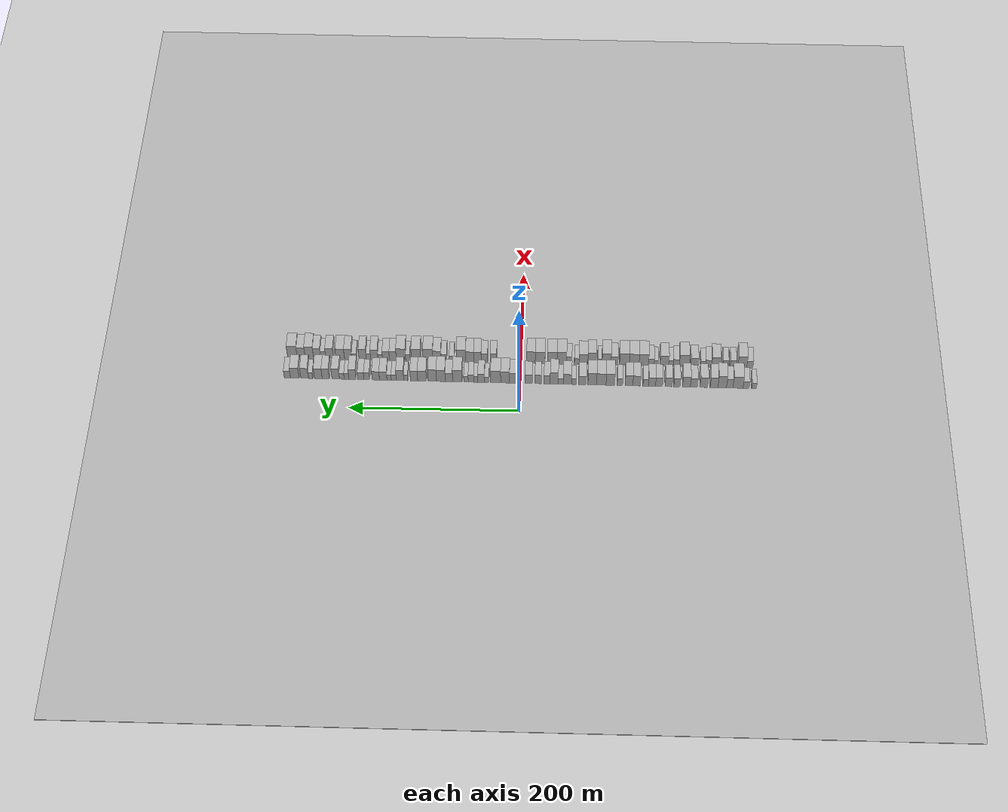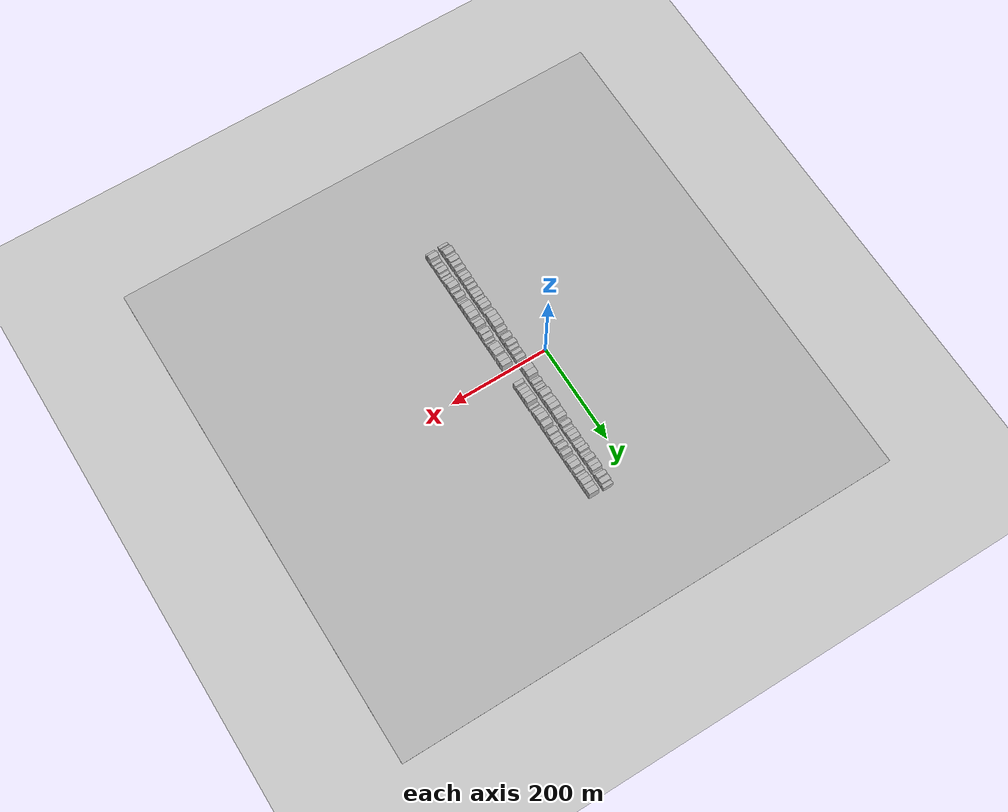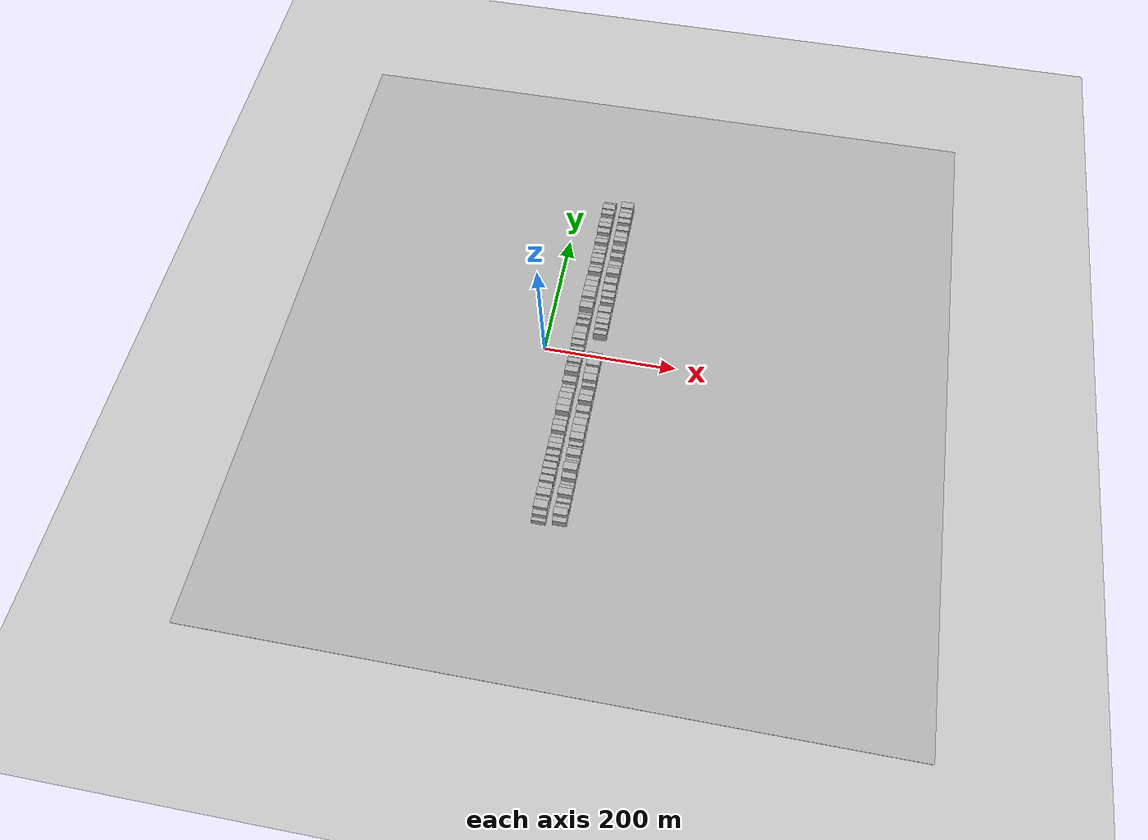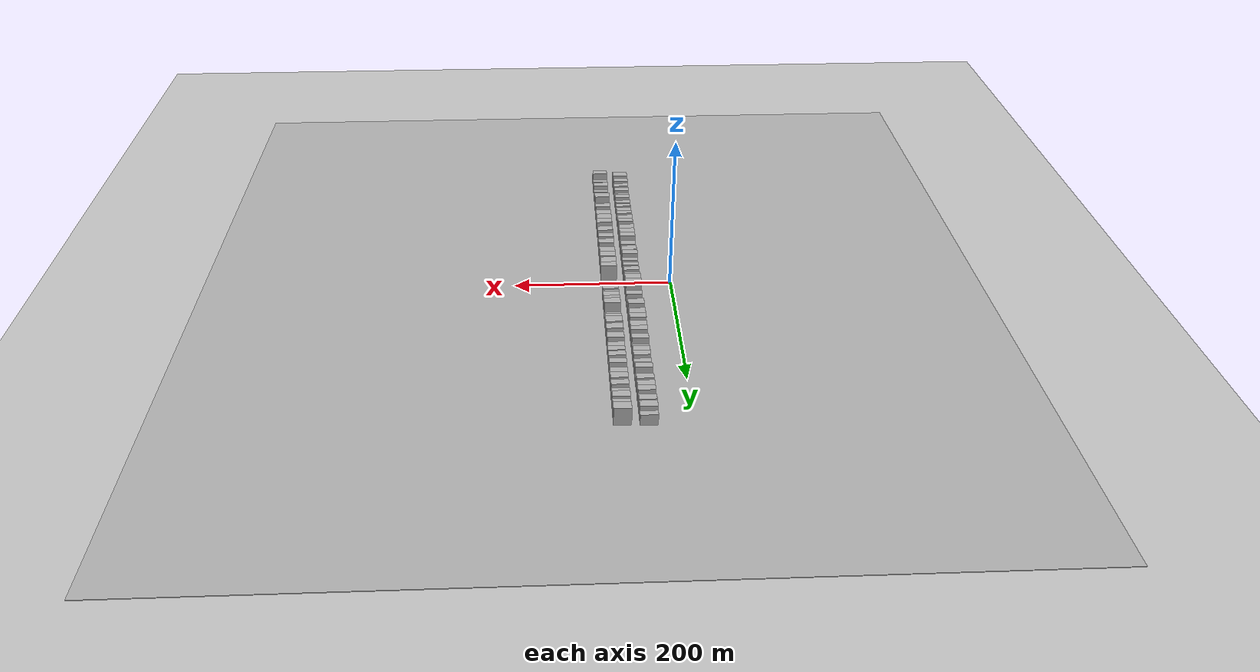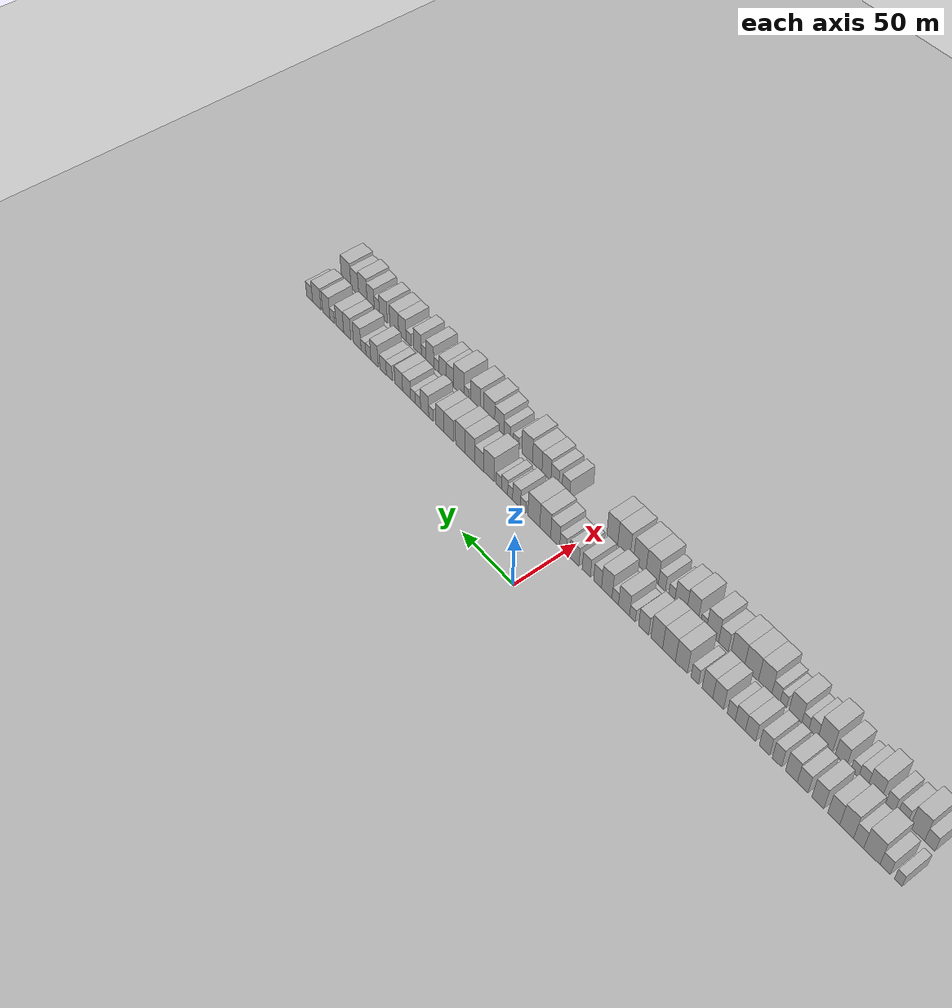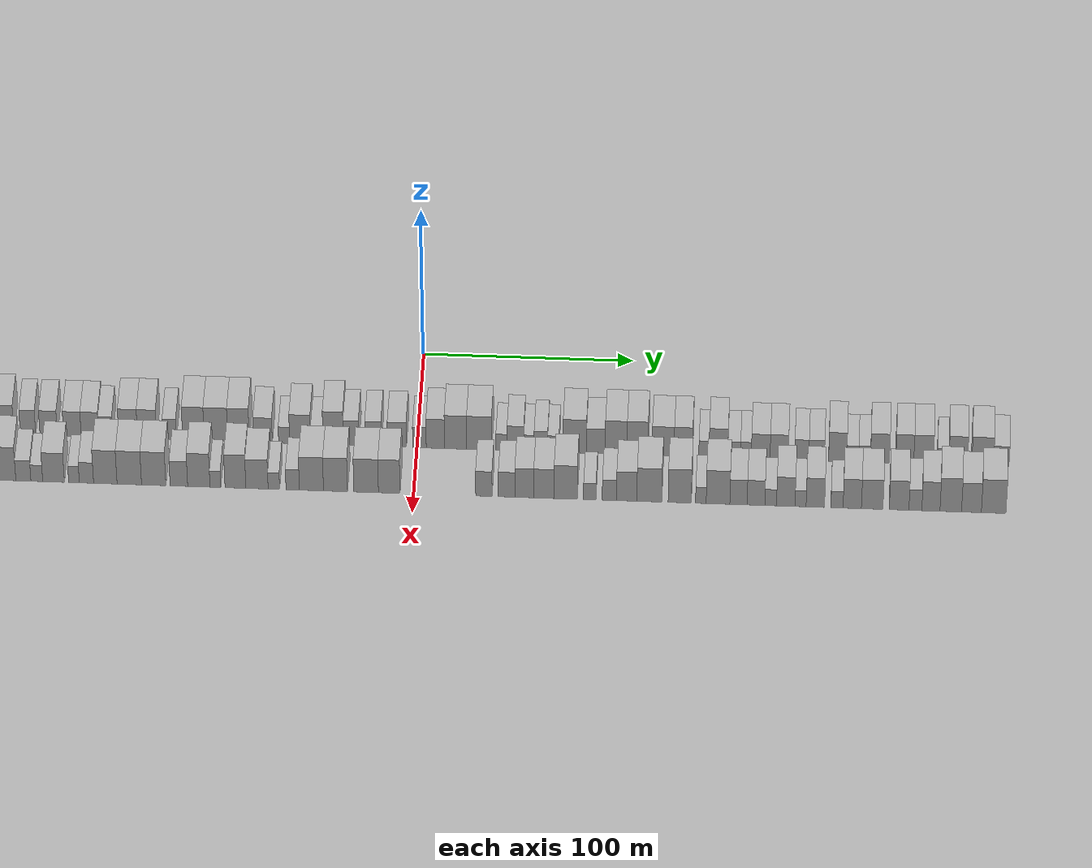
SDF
<?xml version="1.0" encoding="utf-8"?>

<sdf version="1.6">

   <world name="default">

      <gui fullscreen="0">

         <camera name="user_camera">

            <pose>-15 0 4.57585 0 0 0</pose>

            <view_controller>orbit</view_controller>

         </camera>

      </gui>

      <scene>

         <sky>

           <clouds>

             <speed>12</speed>

           </clouds>

         </sky>

         <ambient>0.4 0.4 0.4 1</ambient>

         <background>0.7 0.7 0.7 1</background>

         <shadows>1</shadows>

      </scene>

      <gravity>0 0 -9.8066</gravity>

      <magnetic_field>6e-06 2.3e-05 -4.2e-05</magnetic_field>

      <physics default="0" name="default_physics" type="ode">

         <ode>

            <solver>

               <type>quick</type>

               <iters>10</iters>

               <sor>1.0</sor>

               <use_dynamic_moi_rescaling>0</use_dynamic_moi_rescaling>

            </solver>

            <constraints>

               <cfm>0</cfm>

               <erp>0.2</erp>

               <contact_max_correcting_vel>100</contact_max_correcting_vel>

               <contact_surface_layer>0.001</contact_surface_layer>

            </constraints>

         </ode>

         <max_step_size>0.004</max_step_size>

         <real_time_factor>1</real_time_factor>

         <real_time_update_rate>250</real_time_update_rate>

      </physics>

      <light name="sun" type="directional">

         <cast_shadows>1</cast_shadows>

         <pose>0 0 10 0 0 0</pose>

         <diffuse>0.8 0.8 0.8 1</diffuse>

         <specular>0.2 0.2 0.2 1</specular>

         <attenuation>

            <range>1000</range>

            <constant>0.9</constant>

            <linear>0.01</linear>

            <quadratic>0.001</quadratic>

         </attenuation>

         <direction>-0.5 0.1 -0.9</direction>

      </light>

      <include>

         <name>ground_plane_1</name>

         <uri>model://HANNAS_ground_plane</uri>

         <pose>0 0 0  0 0 0</pose>

      </include>

      <include>

         <name>ground_plane_2</name>

         <uri>model://HANNAS_ground_plane</uri>

         <pose>100 0 0  0 0 0</pose>

      </include>

      <model name="building_1">

         <static>1</static>

         <pose frame="">50.0000 -275.2284 0 0.000000 0.000000 0.000000</pose>

         <link name="link">

            <pose frame="">0 0 6.00 0 0 0</pose>

            <collision name="collision">

               <geometry>

                  <box>

                     <size>20.0000 5.5433 12.0000</size>

                  </box>

               </geometry>

               <max_contacts>10</max_contacts>

               <surface>

                  <contact>

                     <ode/>

                  </contact>

                  <bounce/>

                  <friction>

                     <torsional>

                        <ode/>

                     </torsional>

                     <ode/>

                  </friction>

               </surface>

            </collision>

            <visual name="visual">

               <cast_shadows>0</cast_shadows>

               <geometry>

                  <box>

                     <size>20.0000 5.5433 12.0000</size>

                  </box>

               </geometry>

               <material>

                  <script>

                     <uri>model://HANNAS_wall/materials/scripts</uri>

                     <uri>model://HANNAS_wall/materials/textures</uri>

                     <name>vrc/HANNAS_wall</name>

                  </script>

               </material>

            </visual>

            <self_collide>0</self_collide>

            <enable_wind>0</enable_wind>

            <kinematic>0</kinematic>

         </link>

      </model>

      <model name="building_2">

         <static>1</static>

         <pose frame="">50.0000 -265.7888 0 0.000000 0.000000 0.000000</pose>

         <link name="link">

            <pose frame="">0 0 7.50 0 0 0</pose>

            <collision name="collision">

               <geometry>

                  <box>

                     <size>20.0000 7.3357 15.0000</size>

                  </box>

               </geometry>

               <max_contacts>10</max_contacts>

               <surface>

                  <contact>

                     <ode/>

                  </contact>

                  <bounce/>

                  <friction>

                     <torsional>

                        <ode/>

                     </torsional>

                     <ode/>

                  </friction>

               </surface>

            </collision>

            <visual name="visual">

               <cast_shadows>0</cast_shadows>

               <geometry>

                  <box>

                     <size>20.0000 7.3357 15.0000</size>

                  </box>

               </geometry>

               <material>

                  <script>

                     <uri>model://HANNAS_wall/materials/scripts</uri>

                     <uri>model://HANNAS_wall/materials/textures</uri>

                     <name>vrc/HANNAS_wall</name>

                  </script>

               </material>

            </visual>

            <self_collide>0</self_collide>

            <enable_wind>0</enable_wind>

            <kinematic>0</kinematic>

         </link>

      </model>

      <model name="building_3">

         <static>1</static>

         <pose frame="">50.0000 -256.1935 0 0.000000 0.000000 0.000000</pose>

         <link name="link">

            <pose frame="">0 0 12.00 0 0 0</pose>

            <collision name="collision">

               <geometry>

                  <box>

                     <size>20.0000 11.8549 24.0000</size>

                  </box>

               </geometry>

               <max_contacts>10</max_contacts>

               <surface>

                  <contact>

                     <ode/>

                  </contact>

                  <bounce/>

                  <friction>

                     <torsional>

                        <ode/>

                     </torsional>

                     <ode/>

                  </friction>

               </surface>

            </collision>

            <visual name="visual">

               <cast_shadows>0</cast_shadows>

               <geometry>

                  <box>

                     <size>20.0000 11.8549 24.0000</size>

                  </box>

               </geometry>

               <material>

                  <script>

                     <uri>model://HANNAS_wall/materials/scripts</uri>

                     <uri>model://HANNAS_wall/materials/textures</uri>

                     <name>vrc/HANNAS_wall</name>

                  </script>

               </material>

            </visual>

            <self_collide>0</self_collide>

            <enable_wind>0</enable_wind>

            <kinematic>0</kinematic>

         </link>

      </model>

      <model name="building_4">

         <static>1</static>

         <pose frame="">50.0000 -246.5376 0 0.000000 0.000000 0.000000</pose>

         <link name="link">

            <pose frame="">0 0 9.00 0 0 0</pose>

            <collision name="collision">

               <geometry>

                  <box>

                     <size>20.0000 7.4569 18.0000</size>

                  </box>

               </geometry>

               <max_contacts>10</max_contacts>

               <surface>

                  <contact>

                     <ode/>

                  </contact>

                  <bounce/>

                  <friction>

                     <torsional>

                        <ode/>

                     </torsional>

                     <ode/>

                  </friction>

               </surface>

            </collision>

            <visual name="visual">

               <cast_shadows>0</cast_shadows>

               <geometry>

                  <box>

                     <size>20.0000 7.4569 18.0000</size>

                  </box>

               </geometry>

               <material>

                  <script>

                     <uri>model://HANNAS_wall/materials/scripts</uri>

                     <uri>model://HANNAS_wall/materials/textures</uri>

                     <name>vrc/HANNAS_wall</name>

                  </script>

               </material>

            </visual>

            <self_collide>0</self_collide>

            <enable_wind>0</enable_wind>

            <kinematic>0</kinematic>

         </link>

      </model>

      <model name="building_5">

         <static>1</static>

         <pose frame="">50.0000 -237.7016 0 0.000000 0.000000 0.000000</pose>

         <link name="link">

            <pose frame="">0 0 12.00 0 0 0</pose>

            <collision name="collision">

               <geometry>

                  <box>

                     <size>20.0000 10.2150 24.0000</size>

                  </box>

               </geometry>

               <max_contacts>10</max_contacts>

               <surface>

                  <contact>

                     <ode/>

                  </contact>

                  <bounce/>

                  <friction>

                     <torsional>

                        <ode/>

                     </torsional>

                     <ode/>

                  </friction>

               </surface>

            </collision>

            <visual name="visual">

               <cast_shadows>0</cast_shadows>

               <geometry>

                  <box>

                     <size>20.0000 10.2150 24.0000</size>

                  </box>

               </geometry>

               <material>

                  <script>

                     <uri>model://HANNAS_wall/materials/scripts</uri>

                     <uri>model://HANNAS_wall/materials/textures</uri>

                     <name>vrc/HANNAS_wall</name>

                  </script>

               </material>

            </visual>

            <self_collide>0</self_collide>

            <enable_wind>0</enable_wind>

            <kinematic>0</kinematic>

         </link>

      </model>

      <model name="building_6">

         <static>1</static>

         <pose frame="">50.0000 -228.0764 0 0.000000 0.000000 0.000000</pose>

         <link name="link">

            <pose frame="">0 0 10.50 0 0 0</pose>

            <collision name="collision">

               <geometry>

                  <box>

                     <size>20.0000 9.0354 21.0000</size>

                  </box>

               </geometry>

               <max_contacts>10</max_contacts>

               <surface>

                  <contact>

                     <ode/>

                  </contact>

                  <bounce/>

                  <friction>

                     <torsional>

                        <ode/>

                     </torsional>

                     <ode/>

                  </friction>

               </surface>

            </collision>

            <visual name="visual">

               <cast_shadows>0</cast_shadows>

               <geometry>

                  <box>

                     <size>20.0000 9.0354 21.0000</size>

                  </box>

               </geometry>

               <material>

                  <script>

                     <uri>model://HANNAS_wall/materials/scripts</uri>

                     <uri>model://HANNAS_wall/materials/textures</uri>

                     <name>vrc/HANNAS_wall</name>

                  </script>

               </material>

            </visual>

            <self_collide>0</self_collide>

            <enable_wind>0</enable_wind>

            <kinematic>0</kinematic>

         </link>

      </model>

      <model name="building_7">

         <static>1</static>

         <pose frame="">50.0000 -216.0344 0 0.000000 0.000000 0.000000</pose>

         <link name="link">

            <pose frame="">0 0 10.50 0 0 0</pose>

            <collision name="collision">

               <geometry>

                  <box>

                     <size>20.0000 9.0486 21.0000</size>

                  </box>

               </geometry>

               <max_contacts>10</max_contacts>

               <surface>

                  <contact>

                     <ode/>

                  </contact>

                  <bounce/>

                  <friction>

                     <torsional>

                        <ode/>

                     </torsional>

                     <ode/>

                  </friction>

               </surface>

            </collision>

            <visual name="visual">

               <cast_shadows>0</cast_shadows>

               <geometry>

                  <box>

                     <size>20.0000 9.0486 21.0000</size>

                  </box>

               </geometry>

               <material>

                  <script>

                     <uri>model://HANNAS_wall/materials/scripts</uri>

                     <uri>model://HANNAS_wall/materials/textures</uri>

                     <name>vrc/HANNAS_wall</name>

                  </script>

               </material>

            </visual>

            <self_collide>0</self_collide>

            <enable_wind>0</enable_wind>

            <kinematic>0</kinematic>

         </link>

      </model>

      <model name="building_8">

         <static>1</static>

         <pose frame="">50.0000 -204.3660 0 0.000000 0.000000 0.000000</pose>

         <link name="link">

            <pose frame="">0 0 9.00 0 0 0</pose>

            <collision name="collision">

               <geometry>

                  <box>

                     <size>20.0000 8.2883 18.0000</size>

                  </box>

               </geometry>

               <max_contacts>10</max_contacts>

               <surface>

                  <contact>

                     <ode/>

                  </contact>

                  <bounce/>

                  <friction>

                     <torsional>

                        <ode/>

                     </torsional>

                     <ode/>

                  </friction>

               </surface>

            </collision>

            <visual name="visual">

               <cast_shadows>0</cast_shadows>

               <geometry>

                  <box>

                     <size>20.0000 8.2883 18.0000</size>

                  </box>

               </geometry>

               <material>

                  <script>

                     <uri>model://HANNAS_wall/materials/scripts</uri>

                     <uri>model://HANNAS_wall/materials/textures</uri>

                     <name>vrc/HANNAS_wall</name>

                  </script>

               </material>

            </visual>

            <self_collide>0</self_collide>

            <enable_wind>0</enable_wind>

            <kinematic>0</kinematic>

         </link>

      </model>

      <model name="building_9">

         <static>1</static>

         <pose frame="">50.0000 -195.6271 0 0.000000 0.000000 0.000000</pose>

         <link name="link">

            <pose frame="">0 0 10.50 0 0 0</pose>

            <collision name="collision">

               <geometry>

                  <box>

                     <size>20.0000 9.1893 21.0000</size>

                  </box>

               </geometry>

               <max_contacts>10</max_contacts>

               <surface>

                  <contact>

                     <ode/>

                  </contact>

                  <bounce/>

                  <friction>

                     <torsional>

                        <ode/>

                     </torsional>

                     <ode/>

                  </friction>

               </surface>

            </collision>

            <visual name="visual">

               <cast_shadows>0</cast_shadows>

               <geometry>

                  <box>

                     <size>20.0000 9.1893 21.0000</size>

                  </box>

               </geometry>

               <material>

                  <script>

                     <uri>model://HANNAS_wall/materials/scripts</uri>

                     <uri>model://HANNAS_wall/materials/textures</uri>

                     <name>vrc/HANNAS_wall</name>

                  </script>

               </material>

            </visual>

            <self_collide>0</self_collide>

            <enable_wind>0</enable_wind>

            <kinematic>0</kinematic>

         </link>

      </model>

      <model name="building_10">

         <static>1</static>

         <pose frame="">50.0000 -184.3791 0 0.000000 0.000000 0.000000</pose>

         <link name="link">

            <pose frame="">0 0 9.00 0 0 0</pose>

            <collision name="collision">

               <geometry>

                  <box>

                     <size>20.0000 7.3068 18.0000</size>

                  </box>

               </geometry>

               <max_contacts>10</max_contacts>

               <surface>

                  <contact>

                     <ode/>

                  </contact>

                  <bounce/>

                  <friction>

                     <torsional>

                        <ode/>

                     </torsional>

                     <ode/>

                  </friction>

               </surface>

            </collision>

            <visual name="visual">

               <cast_shadows>0</cast_shadows>

               <geometry>

                  <box>

                     <size>20.0000 7.3068 18.0000</size>

                  </box>

               </geometry>

               <material>

                  <script>

                     <uri>model://HANNAS_wall/materials/scripts</uri>

                     <uri>model://HANNAS_wall/materials/textures</uri>

                     <name>vrc/HANNAS_wall</name>

                  </script>

               </material>

            </visual>

            <self_collide>0</self_collide>

            <enable_wind>0</enable_wind>

            <kinematic>0</kinematic>

         </link>

      </model>

      <model name="building_11">

         <static>1</static>

         <pose frame="">50.0000 -174.5817 0 0.000000 0.000000 0.000000</pose>

         <link name="link">

            <pose frame="">0 0 9.00 0 0 0</pose>

            <collision name="collision">

               <geometry>

                  <box>

                     <size>20.0000 8.2879 18.0000</size>

                  </box>

               </geometry>

               <max_contacts>10</max_contacts>

               <surface>

                  <contact>

                     <ode/>

                  </contact>

                  <bounce/>

                  <friction>

                     <torsional>

                        <ode/>

                     </torsional>

                     <ode/>

                  </friction>

               </surface>

            </collision>

            <visual name="visual">

               <cast_shadows>0</cast_shadows>

               <geometry>

                  <box>

                     <size>20.0000 8.2879 18.0000</size>

                  </box>

               </geometry>

               <material>

                  <script>

                     <uri>model://HANNAS_wall/materials/scripts</uri>

                     <uri>model://HANNAS_wall/materials/textures</uri>

                     <name>vrc/HANNAS_wall</name>

                  </script>

               </material>

            </visual>

            <self_collide>0</self_collide>

            <enable_wind>0</enable_wind>

            <kinematic>0</kinematic>

         </link>

      </model>

      <model name="building_12">

         <static>1</static>

         <pose frame="">50.0000 -163.2917 0 0.000000 0.000000 0.000000</pose>

         <link name="link">

            <pose frame="">0 0 9.00 0 0 0</pose>

            <collision name="collision">

               <geometry>

                  <box>

                     <size>20.0000 8.2921 18.0000</size>

                  </box>

               </geometry>

               <max_contacts>10</max_contacts>

               <surface>

                  <contact>

                     <ode/>

                  </contact>

                  <bounce/>

                  <friction>

                     <torsional>

                        <ode/>

                     </torsional>

                     <ode/>

                  </friction>

               </surface>

            </collision>

            <visual name="visual">

               <cast_shadows>0</cast_shadows>

               <geometry>

                  <box>

                     <size>20.0000 8.2921 18.0000</size>

                  </box>

               </geometry>

               <material>

                  <script>

                     <uri>model://HANNAS_wall/materials/scripts</uri>

                     <uri>model://HANNAS_wall/materials/textures</uri>

                     <name>vrc/HANNAS_wall</name>

                  </script>

               </material>

            </visual>

            <self_collide>0</self_collide>

            <enable_wind>0</enable_wind>

            <kinematic>0</kinematic>

         </link>

      </model>

      <model name="building_13">

         <static>1</static>

         <pose frame="">50.0000 -154.9882 0 0.000000 0.000000 0.000000</pose>

         <link name="link">

            <pose frame="">0 0 9.00 0 0 0</pose>

            <collision name="collision">

               <geometry>

                  <box>

                     <size>20.0000 8.3149 18.0000</size>

                  </box>

               </geometry>

               <max_contacts>10</max_contacts>

               <surface>

                  <contact>

                     <ode/>

                  </contact>

                  <bounce/>

                  <friction>

                     <torsional>

                        <ode/>

                     </torsional>

                     <ode/>

                  </friction>

               </surface>

            </collision>

            <visual name="visual">

               <cast_shadows>0</cast_shadows>

               <geometry>

                  <box>

                     <size>20.0000 8.3149 18.0000</size>

                  </box>

               </geometry>

               <material>

                  <script>

                     <uri>model://HANNAS_wall/materials/scripts</uri>

                     <uri>model://HANNAS_wall/materials/textures</uri>

                     <name>vrc/HANNAS_wall</name>

                  </script>

               </material>

            </visual>

            <self_collide>0</self_collide>

            <enable_wind>0</enable_wind>

            <kinematic>0</kinematic>

         </link>

      </model>

      <model name="building_14">

         <static>1</static>

         <pose frame="">50.0000 -147.5712 0 0.000000 0.000000 0.000000</pose>

         <link name="link">

            <pose frame="">0 0 7.50 0 0 0</pose>

            <collision name="collision">

               <geometry>

                  <box>

                     <size>20.0000 6.5192 15.0000</size>

                  </box>

               </geometry>

               <max_contacts>10</max_contacts>

               <surface>

                  <contact>

                     <ode/>

                  </contact>

                  <bounce/>

                  <friction>

                     <torsional>

                        <ode/>

                     </torsional>

                     <ode/>

                  </friction>

               </surface>

            </collision>

            <visual name="visual">

               <cast_shadows>0</cast_shadows>

               <geometry>

                  <box>

                     <size>20.0000 6.5192 15.0000</size>

                  </box>

               </geometry>

               <material>

                  <script>

                     <uri>model://HANNAS_wall/materials/scripts</uri>

                     <uri>model://HANNAS_wall/materials/textures</uri>

                     <name>vrc/HANNAS_wall</name>

                  </script>

               </material>

            </visual>

            <self_collide>0</self_collide>

            <enable_wind>0</enable_wind>

            <kinematic>0</kinematic>

         </link>

      </model>

      <model name="building_15">

         <static>1</static>

         <pose frame="">50.0000 -136.8504 0 0.000000 0.000000 0.000000</pose>

         <link name="link">

            <pose frame="">0 0 10.50 0 0 0</pose>

            <collision name="collision">

               <geometry>

                  <box>

                     <size>20.0000 8.9223 21.0000</size>

                  </box>

               </geometry>

               <max_contacts>10</max_contacts>

               <surface>

                  <contact>

                     <ode/>

                  </contact>

                  <bounce/>

                  <friction>

                     <torsional>

                        <ode/>

                     </torsional>

                     <ode/>

                  </friction>

               </surface>

            </collision>

            <visual name="visual">

               <cast_shadows>0</cast_shadows>

               <geometry>

                  <box>

                     <size>20.0000 8.9223 21.0000</size>

                  </box>

               </geometry>

               <material>

                  <script>

                     <uri>model://HANNAS_wall/materials/scripts</uri>

                     <uri>model://HANNAS_wall/materials/textures</uri>

                     <name>vrc/HANNAS_wall</name>

                  </script>

               </material>

            </visual>

            <self_collide>0</self_collide>

            <enable_wind>0</enable_wind>

            <kinematic>0</kinematic>

         </link>

      </model>

      <model name="building_16">

         <static>1</static>

         <pose frame="">50.0000 -127.8862 0 0.000000 0.000000 0.000000</pose>

         <link name="link">

            <pose frame="">0 0 10.50 0 0 0</pose>

            <collision name="collision">

               <geometry>

                  <box>

                     <size>20.0000 9.0061 21.0000</size>

                  </box>

               </geometry>

               <max_contacts>10</max_contacts>

               <surface>

                  <contact>

                     <ode/>

                  </contact>

                  <bounce/>

                  <friction>

                     <torsional>

                        <ode/>

                     </torsional>

                     <ode/>

                  </friction>

               </surface>

            </collision>

            <visual name="visual">

               <cast_shadows>0</cast_shadows>

               <geometry>

                  <box>

                     <size>20.0000 9.0061 21.0000</size>

                  </box>

               </geometry>

               <material>

                  <script>

                     <uri>model://HANNAS_wall/materials/scripts</uri>

                     <uri>model://HANNAS_wall/materials/textures</uri>

                     <name>vrc/HANNAS_wall</name>

                  </script>

               </material>

            </visual>

            <self_collide>0</self_collide>

            <enable_wind>0</enable_wind>

            <kinematic>0</kinematic>

         </link>

      </model>

      <model name="building_17">

         <static>1</static>

         <pose frame="">50.0000 -117.1879 0 0.000000 0.000000 0.000000</pose>

         <link name="link">

            <pose frame="">0 0 7.50 0 0 0</pose>

            <collision name="collision">

               <geometry>

                  <box>

                     <size>20.0000 6.3906 15.0000</size>

                  </box>

               </geometry>

               <max_contacts>10</max_contacts>

               <surface>

                  <contact>

                     <ode/>

                  </contact>

                  <bounce/>

                  <friction>

                     <torsional>

                        <ode/>

                     </torsional>

                     <ode/>

                  </friction>

               </surface>

            </collision>

            <visual name="visual">

               <cast_shadows>0</cast_shadows>

               <geometry>

                  <box>

                     <size>20.0000 6.3906 15.0000</size>

                  </box>

               </geometry>

               <material>

                  <script>

                     <uri>model://HANNAS_wall/materials/scripts</uri>

                     <uri>model://HANNAS_wall/materials/textures</uri>

                     <name>vrc/HANNAS_wall</name>

                  </script>

               </material>

            </visual>

            <self_collide>0</self_collide>

            <enable_wind>0</enable_wind>

            <kinematic>0</kinematic>

         </link>

      </model>

      <model name="building_18">

         <static>1</static>

         <pose frame="">50.0000 -105.8745 0 0.000000 0.000000 0.000000</pose>

         <link name="link">

            <pose frame="">0 0 12.00 0 0 0</pose>

            <collision name="collision">

               <geometry>

                  <box>

                     <size>20.0000 10.2362 24.0000</size>

                  </box>

               </geometry>

               <max_contacts>10</max_contacts>

               <surface>

                  <contact>

                     <ode/>

                  </contact>

                  <bounce/>

                  <friction>

                     <torsional>

                        <ode/>

                     </torsional>

                     <ode/>

                  </friction>

               </surface>

            </collision>

            <visual name="visual">

               <cast_shadows>0</cast_shadows>

               <geometry>

                  <box>

                     <size>20.0000 10.2362 24.0000</size>

                  </box>

               </geometry>

               <material>

                  <script>

                     <uri>model://HANNAS_wall/materials/scripts</uri>

                     <uri>model://HANNAS_wall/materials/textures</uri>

                     <name>vrc/HANNAS_wall</name>

                  </script>

               </material>

            </visual>

            <self_collide>0</self_collide>

            <enable_wind>0</enable_wind>

            <kinematic>0</kinematic>

         </link>

      </model>

      <model name="building_19">

         <static>1</static>

         <pose frame="">50.0000 -95.1828 0 0.000000 0.000000 0.000000</pose>

         <link name="link">

            <pose frame="">0 0 12.00 0 0 0</pose>

            <collision name="collision">

               <geometry>

                  <box>

                     <size>20.0000 11.1471 24.0000</size>

                  </box>

               </geometry>

               <max_contacts>10</max_contacts>

               <surface>

                  <contact>

                     <ode/>

                  </contact>

                  <bounce/>

                  <friction>

                     <torsional>

                        <ode/>

                     </torsional>

                     <ode/>

                  </friction>

               </surface>

            </collision>

            <visual name="visual">

               <cast_shadows>0</cast_shadows>

               <geometry>

                  <box>

                     <size>20.0000 11.1471 24.0000</size>

                  </box>

               </geometry>

               <material>

                  <script>

                     <uri>model://HANNAS_wall/materials/scripts</uri>

                     <uri>model://HANNAS_wall/materials/textures</uri>

                     <name>vrc/HANNAS_wall</name>

                  </script>

               </material>

            </visual>

            <self_collide>0</self_collide>

            <enable_wind>0</enable_wind>

            <kinematic>0</kinematic>

         </link>

      </model>

      <model name="building_20">

         <static>1</static>

         <pose frame="">50.0000 -84.5005 0 0.000000 0.000000 0.000000</pose>

         <link name="link">

            <pose frame="">0 0 12.00 0 0 0</pose>

            <collision name="collision">

               <geometry>

                  <box>

                     <size>20.0000 10.2175 24.0000</size>

                  </box>

               </geometry>

               <max_contacts>10</max_contacts>

               <surface>

                  <contact>

                     <ode/>

                  </contact>

                  <bounce/>

                  <friction>

                     <torsional>

                        <ode/>

                     </torsional>

                     <ode/>

                  </friction>

               </surface>

            </collision>

            <visual name="visual">

               <cast_shadows>0</cast_shadows>

               <geometry>

                  <box>

                     <size>20.0000 10.2175 24.0000</size>

                  </box>

               </geometry>

               <material>

                  <script>

                     <uri>model://HANNAS_wall/materials/scripts</uri>

                     <uri>model://HANNAS_wall/materials/textures</uri>

                     <name>vrc/HANNAS_wall</name>

                  </script>

               </material>

            </visual>

            <self_collide>0</self_collide>

            <enable_wind>0</enable_wind>

            <kinematic>0</kinematic>

         </link>

      </model>

      <model name="building_21">

         <static>1</static>

         <pose frame="">50.0000 -72.9549 0 0.000000 0.000000 0.000000</pose>

         <link name="link">

            <pose frame="">0 0 9.00 0 0 0</pose>

            <collision name="collision">

               <geometry>

                  <box>

                     <size>20.0000 8.8736 18.0000</size>

                  </box>

               </geometry>

               <max_contacts>10</max_contacts>

               <surface>

                  <contact>

                     <ode/>

                  </contact>

                  <bounce/>

                  <friction>

                     <torsional>

                        <ode/>

                     </torsional>

                     <ode/>

                  </friction>

               </surface>

            </collision>

            <visual name="visual">

               <cast_shadows>0</cast_shadows>

               <geometry>

                  <box>

                     <size>20.0000 8.8736 18.0000</size>

                  </box>

               </geometry>

               <material>

                  <script>

                     <uri>model://HANNAS_wall/materials/scripts</uri>

                     <uri>model://HANNAS_wall/materials/textures</uri>

                     <name>vrc/HANNAS_wall</name>

                  </script>

               </material>

            </visual>

            <self_collide>0</self_collide>

            <enable_wind>0</enable_wind>

            <kinematic>0</kinematic>

         </link>

      </model>

      <model name="building_22">

         <static>1</static>

         <pose frame="">50.0000 -62.8980 0 0.000000 0.000000 0.000000</pose>

         <link name="link">

            <pose frame="">0 0 6.00 0 0 0</pose>

            <collision name="collision">

               <geometry>

                  <box>

                     <size>20.0000 5.2403 12.0000</size>

                  </box>

               </geometry>

               <max_contacts>10</max_contacts>

               <surface>

                  <contact>

                     <ode/>

                  </contact>

                  <bounce/>

                  <friction>

                     <torsional>

                        <ode/>

                     </torsional>

                     <ode/>

                  </friction>

               </surface>

            </collision>

            <visual name="visual">

               <cast_shadows>0</cast_shadows>

               <geometry>

                  <box>

                     <size>20.0000 5.2403 12.0000</size>

                  </box>

               </geometry>

               <material>

                  <script>

                     <uri>model://HANNAS_wall/materials/scripts</uri>

                     <uri>model://HANNAS_wall/materials/textures</uri>

                     <name>vrc/HANNAS_wall</name>

                  </script>

               </material>

            </visual>

            <self_collide>0</self_collide>

            <enable_wind>0</enable_wind>

            <kinematic>0</kinematic>

         </link>

      </model>

      <model name="building_23">

         <static>1</static>

         <pose frame="">50.0000 -55.2958 0 0.000000 0.000000 0.000000</pose>

         <link name="link">

            <pose frame="">0 0 10.50 0 0 0</pose>

            <collision name="collision">

               <geometry>

                  <box>

                     <size>20.0000 9.9641 21.0000</size>

                  </box>

               </geometry>

               <max_contacts>10</max_contacts>

               <surface>

                  <contact>

                     <ode/>

                  </contact>

                  <bounce/>

                  <friction>

                     <torsional>

                        <ode/>

                     </torsional>

                     <ode/>

                  </friction>

               </surface>

            </collision>

            <visual name="visual">

               <cast_shadows>0</cast_shadows>

               <geometry>

                  <box>

                     <size>20.0000 9.9641 21.0000</size>

                  </box>

               </geometry>

               <material>

                  <script>

                     <uri>model://HANNAS_wall/materials/scripts</uri>

                     <uri>model://HANNAS_wall/materials/textures</uri>

                     <name>vrc/HANNAS_wall</name>

                  </script>

               </material>

            </visual>

            <self_collide>0</self_collide>

            <enable_wind>0</enable_wind>

            <kinematic>0</kinematic>

         </link>

      </model>

      <model name="building_24">

         <static>1</static>

         <pose frame="">50.0000 -47.3811 0 0.000000 0.000000 0.000000</pose>

         <link name="link">

            <pose frame="">0 0 6.00 0 0 0</pose>

            <collision name="collision">

               <geometry>

                  <box>

                     <size>20.0000 5.8652 12.0000</size>

                  </box>

               </geometry>

               <max_contacts>10</max_contacts>

               <surface>

                  <contact>

                     <ode/>

                  </contact>

                  <bounce/>

                  <friction>

                     <torsional>

                        <ode/>

                     </torsional>

                     <ode/>

                  </friction>

               </surface>

            </collision>

            <visual name="visual">

               <cast_shadows>0</cast_shadows>

               <geometry>

                  <box>

                     <size>20.0000 5.8652 12.0000</size>

                  </box>

               </geometry>

               <material>

                  <script>

                     <uri>model://HANNAS_wall/materials/scripts</uri>

                     <uri>model://HANNAS_wall/materials/textures</uri>

                     <name>vrc/HANNAS_wall</name>

                  </script>

               </material>

            </visual>

            <self_collide>0</self_collide>

            <enable_wind>0</enable_wind>

            <kinematic>0</kinematic>

         </link>

      </model>

      <model name="building_25">

         <static>1</static>

         <pose frame="">50.0000 -39.6424 0 0.000000 0.000000 0.000000</pose>

         <link name="link">

            <pose frame="">0 0 12.00 0 0 0</pose>

            <collision name="collision">

               <geometry>

                  <box>

                     <size>20.0000 9.6122 24.0000</size>

                  </box>

               </geometry>

               <max_contacts>10</max_contacts>

               <surface>

                  <contact>

                     <ode/>

                  </contact>

                  <bounce/>

                  <friction>

                     <torsional>

                        <ode/>

                     </torsional>

                     <ode/>

                  </friction>

               </surface>

            </collision>

            <visual name="visual">

               <cast_shadows>0</cast_shadows>

               <geometry>

                  <box>

                     <size>20.0000 9.6122 24.0000</size>

                  </box>

               </geometry>

               <material>

                  <script>

                     <uri>model://HANNAS_wall/materials/scripts</uri>

                     <uri>model://HANNAS_wall/materials/textures</uri>

                     <name>vrc/HANNAS_wall</name>

                  </script>

               </material>

            </visual>

            <self_collide>0</self_collide>

            <enable_wind>0</enable_wind>

            <kinematic>0</kinematic>

         </link>

      </model>

      <model name="building_26">

         <static>1</static>

         <pose frame="">50.0000 -31.1935 0 0.000000 0.000000 0.000000</pose>

         <link name="link">

            <pose frame="">0 0 9.00 0 0 0</pose>

            <collision name="collision">

               <geometry>

                  <box>

                     <size>20.0000 7.2858 18.0000</size>

                  </box>

               </geometry>

               <max_contacts>10</max_contacts>

               <surface>

                  <contact>

                     <ode/>

                  </contact>

                  <bounce/>

                  <friction>

                     <torsional>

                        <ode/>

                     </torsional>

                     <ode/>

                  </friction>

               </surface>

            </collision>

            <visual name="visual">

               <cast_shadows>0</cast_shadows>

               <geometry>

                  <box>

                     <size>20.0000 7.2858 18.0000</size>

                  </box>

               </geometry>

               <material>

                  <script>

                     <uri>model://HANNAS_wall/materials/scripts</uri>

                     <uri>model://HANNAS_wall/materials/textures</uri>

                     <name>vrc/HANNAS_wall</name>

                  </script>

               </material>

            </visual>

            <self_collide>0</self_collide>

            <enable_wind>0</enable_wind>

            <kinematic>0</kinematic>

         </link>

      </model>

      <model name="building_27">

         <static>1</static>

         <pose frame="">50.0000 -20.7220 0 0.000000 0.000000 0.000000</pose>

         <link name="link">

            <pose frame="">0 0 9.00 0 0 0</pose>

            <collision name="collision">

               <geometry>

                  <box>

                     <size>20.0000 7.6572 18.0000</size>

                  </box>

               </geometry>

               <max_contacts>10</max_contacts>

               <surface>

                  <contact>

                     <ode/>

                  </contact>

                  <bounce/>

                  <friction>

                     <torsional>

                        <ode/>

                     </torsional>

                     <ode/>

                  </friction>

               </surface>

            </collision>

            <visual name="visual">

               <cast_shadows>0</cast_shadows>

               <geometry>

                  <box>

                     <size>20.0000 7.6572 18.0000</size>

                  </box>

               </geometry>

               <material>

                  <script>

                     <uri>model://HANNAS_wall/materials/scripts</uri>

                     <uri>model://HANNAS_wall/materials/textures</uri>

                     <name>vrc/HANNAS_wall</name>

                  </script>

               </material>

            </visual>

            <self_collide>0</self_collide>

            <enable_wind>0</enable_wind>

            <kinematic>0</kinematic>

         </link>

      </model>

      <model name="building_28">

         <static>1</static>

         <pose frame="">50.0000 -9.4502 0 0.000000 0.000000 0.000000</pose>

         <link name="link">

            <pose frame="">0 0 9.00 0 0 0</pose>

            <collision name="collision">

               <geometry>

                  <box>

                     <size>20.0000 8.8863 18.0000</size>

                  </box>

               </geometry>

               <max_contacts>10</max_contacts>

               <surface>

                  <contact>

                     <ode/>

                  </contact>

                  <bounce/>

                  <friction>

                     <torsional>

                        <ode/>

                     </torsional>

                     <ode/>

                  </friction>

               </surface>

            </collision>

            <visual name="visual">

               <cast_shadows>0</cast_shadows>

               <geometry>

                  <box>

                     <size>20.0000 8.8863 18.0000</size>

                  </box>

               </geometry>

               <material>

                  <script>

                     <uri>model://HANNAS_wall/materials/scripts</uri>

                     <uri>model://HANNAS_wall/materials/textures</uri>

                     <name>vrc/HANNAS_wall</name>

                  </script>

               </material>

            </visual>

            <self_collide>0</self_collide>

            <enable_wind>0</enable_wind>

            <kinematic>0</kinematic>

         </link>

      </model>

      <model name="building_29">

         <static>1</static>

         <pose frame="">50.0000 1.1949 0 0.000000 0.000000 0.000000</pose>

         <link name="link">

            <pose frame="">0 0 7.50 0 0 0</pose>

            <collision name="collision">

               <geometry>

                  <box>

                     <size>20.0000 6.4039 15.0000</size>

                  </box>

               </geometry>

               <max_contacts>10</max_contacts>

               <surface>

                  <contact>

                     <ode/>

                  </contact>

                  <bounce/>

                  <friction>

                     <torsional>

                        <ode/>

                     </torsional>

                     <ode/>

                  </friction>

               </surface>

            </collision>

            <visual name="visual">

               <cast_shadows>0</cast_shadows>

               <geometry>

                  <box>

                     <size>20.0000 6.4039 15.0000</size>

                  </box>

               </geometry>

               <material>

                  <script>

                     <uri>model://HANNAS_wall/materials/scripts</uri>

                     <uri>model://HANNAS_wall/materials/textures</uri>

                     <name>vrc/HANNAS_wall</name>

                  </script>

               </material>

            </visual>

            <self_collide>0</self_collide>

            <enable_wind>0</enable_wind>

            <kinematic>0</kinematic>

         </link>

      </model>

      <model name="building_30">

         <static>1</static>

         <pose frame="">50.0000 8.7194 0 0.000000 0.000000 0.000000</pose>

         <link name="link">

            <pose frame="">0 0 10.50 0 0 0</pose>

            <collision name="collision">

               <geometry>

                  <box>

                     <size>20.0000 8.6451 21.0000</size>

                  </box>

               </geometry>

               <max_contacts>10</max_contacts>

               <surface>

                  <contact>

                     <ode/>

                  </contact>

                  <bounce/>

                  <friction>

                     <torsional>

                        <ode/>

                     </torsional>

                     <ode/>

                  </friction>

               </surface>

            </collision>

            <visual name="visual">

               <cast_shadows>0</cast_shadows>

               <geometry>

                  <box>

                     <size>20.0000 8.6451 21.0000</size>

                  </box>

               </geometry>

               <material>

                  <script>

                     <uri>model://HANNAS_wall/materials/scripts</uri>

                     <uri>model://HANNAS_wall/materials/textures</uri>

                     <name>vrc/HANNAS_wall</name>

                  </script>

               </material>

            </visual>

            <self_collide>0</self_collide>

            <enable_wind>0</enable_wind>

            <kinematic>0</kinematic>

         </link>

      </model>

      <model name="building_31">

         <static>1</static>

         <pose frame="">50.0000 18.3045 0 0.000000 0.000000 0.000000</pose>

         <link name="link">

            <pose frame="">0 0 12.00 0 0 0</pose>

            <collision name="collision">

               <geometry>

                  <box>

                     <size>20.0000 10.5250 24.0000</size>

                  </box>

               </geometry>

               <max_contacts>10</max_contacts>

               <surface>

                  <contact>

                     <ode/>

                  </contact>

                  <bounce/>

                  <friction>

                     <torsional>

                        <ode/>

                     </torsional>

                     <ode/>

                  </friction>

               </surface>

            </collision>

            <visual name="visual">

               <cast_shadows>0</cast_shadows>

               <geometry>

                  <box>

                     <size>20.0000 10.5250 24.0000</size>

                  </box>

               </geometry>

               <material>

                  <script>

                     <uri>model://HANNAS_wall/materials/scripts</uri>

                     <uri>model://HANNAS_wall/materials/textures</uri>

                     <name>vrc/HANNAS_wall</name>

                  </script>

               </material>

            </visual>

            <self_collide>0</self_collide>

            <enable_wind>0</enable_wind>

            <kinematic>0</kinematic>

         </link>

      </model>

      <model name="building_32">

         <static>1</static>

         <pose frame="">50.0000 29.4682 0 0.000000 0.000000 0.000000</pose>

         <link name="link">

            <pose frame="">0 0 12.00 0 0 0</pose>

            <collision name="collision">

               <geometry>

                  <box>

                     <size>20.0000 11.8026 24.0000</size>

                  </box>

               </geometry>

               <max_contacts>10</max_contacts>

               <surface>

                  <contact>

                     <ode/>

                  </contact>

                  <bounce/>

                  <friction>

                     <torsional>

                        <ode/>

                     </torsional>

                     <ode/>

                  </friction>

               </surface>

            </collision>

            <visual name="visual">

               <cast_shadows>0</cast_shadows>

               <geometry>

                  <box>

                     <size>20.0000 11.8026 24.0000</size>

                  </box>

               </geometry>

               <material>

                  <script>

                     <uri>model://HANNAS_wall/materials/scripts</uri>

                     <uri>model://HANNAS_wall/materials/textures</uri>

                     <name>vrc/HANNAS_wall</name>

                  </script>

               </material>

            </visual>

            <self_collide>0</self_collide>

            <enable_wind>0</enable_wind>

            <kinematic>0</kinematic>

         </link>

      </model>

      <model name="building_33">

         <static>1</static>

         <pose frame="">50.0000 40.0269 0 0.000000 0.000000 0.000000</pose>

         <link name="link">

            <pose frame="">0 0 6.00 0 0 0</pose>

            <collision name="collision">

               <geometry>

                  <box>

                     <size>20.0000 5.3147 12.0000</size>

                  </box>

               </geometry>

               <max_contacts>10</max_contacts>

               <surface>

                  <contact>

                     <ode/>

                  </contact>

                  <bounce/>

                  <friction>

                     <torsional>

                        <ode/>

                     </torsional>

                     <ode/>

                  </friction>

               </surface>

            </collision>

            <visual name="visual">

               <cast_shadows>0</cast_shadows>

               <geometry>

                  <box>

                     <size>20.0000 5.3147 12.0000</size>

                  </box>

               </geometry>

               <material>

                  <script>

                     <uri>model://HANNAS_wall/materials/scripts</uri>

                     <uri>model://HANNAS_wall/materials/textures</uri>

                     <name>vrc/HANNAS_wall</name>

                  </script>

               </material>

            </visual>

            <self_collide>0</self_collide>

            <enable_wind>0</enable_wind>

            <kinematic>0</kinematic>

         </link>

      </model>

      <model name="building_34">

         <static>1</static>

         <pose frame="">50.0000 46.6303 0 0.000000 0.000000 0.000000</pose>

         <link name="link">

            <pose frame="">0 0 9.00 0 0 0</pose>

            <collision name="collision">

               <geometry>

                  <box>

                     <size>20.0000 7.8922 18.0000</size>

                  </box>

               </geometry>

               <max_contacts>10</max_contacts>

               <surface>

                  <contact>

                     <ode/>

                  </contact>

                  <bounce/>

                  <friction>

                     <torsional>

                        <ode/>

                     </torsional>

                     <ode/>

                  </friction>

               </surface>

            </collision>

            <visual name="visual">

               <cast_shadows>0</cast_shadows>

               <geometry>

                  <box>

                     <size>20.0000 7.8922 18.0000</size>

                  </box>

               </geometry>

               <material>

                  <script>

                     <uri>model://HANNAS_wall/materials/scripts</uri>

                     <uri>model://HANNAS_wall/materials/textures</uri>

                     <name>vrc/HANNAS_wall</name>

                  </script>

               </material>

            </visual>

            <self_collide>0</self_collide>

            <enable_wind>0</enable_wind>

            <kinematic>0</kinematic>

         </link>

      </model>

      <model name="building_35">

         <static>1</static>

         <pose frame="">50.0000 53.0246 0 0.000000 0.000000 0.000000</pose>

         <link name="link">

            <pose frame="">0 0 6.00 0 0 0</pose>

            <collision name="collision">

               <geometry>

                  <box>

                     <size>20.0000 4.8964 12.0000</size>

                  </box>

               </geometry>

               <max_contacts>10</max_contacts>

               <surface>

                  <contact>

                     <ode/>

                  </contact>

                  <bounce/>

                  <friction>

                     <torsional>

                        <ode/>

                     </torsional>

                     <ode/>

                  </friction>

               </surface>

            </collision>

            <visual name="visual">

               <cast_shadows>0</cast_shadows>

               <geometry>

                  <box>

                     <size>20.0000 4.8964 12.0000</size>

                  </box>

               </geometry>

               <material>

                  <script>

                     <uri>model://HANNAS_wall/materials/scripts</uri>

                     <uri>model://HANNAS_wall/materials/textures</uri>

                     <name>vrc/HANNAS_wall</name>

                  </script>

               </material>

            </visual>

            <self_collide>0</self_collide>

            <enable_wind>0</enable_wind>

            <kinematic>0</kinematic>

         </link>

      </model>

      <model name="building_36">

         <static>1</static>

         <pose frame="">50.0000 58.6801 0 0.000000 0.000000 0.000000</pose>

         <link name="link">

            <pose frame="">0 0 7.50 0 0 0</pose>

            <collision name="collision">

               <geometry>

                  <box>

                     <size>20.0000 6.4146 15.0000</size>

                  </box>

               </geometry>

               <max_contacts>10</max_contacts>

               <surface>

                  <contact>

                     <ode/>

                  </contact>

                  <bounce/>

                  <friction>

                     <torsional>

                        <ode/>

                     </torsional>

                     <ode/>

                  </friction>

               </surface>

            </collision>

            <visual name="visual">

               <cast_shadows>0</cast_shadows>

               <geometry>

                  <box>

                     <size>20.0000 6.4146 15.0000</size>

                  </box>

               </geometry>

               <material>

                  <script>

                     <uri>model://HANNAS_wall/materials/scripts</uri>

                     <uri>model://HANNAS_wall/materials/textures</uri>

                     <name>vrc/HANNAS_wall</name>

                  </script>

               </material>

            </visual>

            <self_collide>0</self_collide>

            <enable_wind>0</enable_wind>

            <kinematic>0</kinematic>

         </link>

      </model>

      <model name="building_37">

         <static>1</static>

         <pose frame="">50.0000 64.5308 0 0.000000 0.000000 0.000000</pose>

         <link name="link">

            <pose frame="">0 0 6.00 0 0 0</pose>

            <collision name="collision">

               <geometry>

                  <box>

                     <size>20.0000 5.2868 12.0000</size>

                  </box>

               </geometry>

               <max_contacts>10</max_contacts>

               <surface>

                  <contact>

                     <ode/>

                  </contact>

                  <bounce/>

                  <friction>

                     <torsional>

                        <ode/>

                     </torsional>

                     <ode/>

                  </friction>

               </surface>

            </collision>

            <visual name="visual">

               <cast_shadows>0</cast_shadows>

               <geometry>

                  <box>

                     <size>20.0000 5.2868 12.0000</size>

                  </box>

               </geometry>

               <material>

                  <script>

                     <uri>model://HANNAS_wall/materials/scripts</uri>

                     <uri>model://HANNAS_wall/materials/textures</uri>

                     <name>vrc/HANNAS_wall</name>

                  </script>

               </material>

            </visual>

            <self_collide>0</self_collide>

            <enable_wind>0</enable_wind>

            <kinematic>0</kinematic>

         </link>

      </model>

      <model name="building_38">

         <static>1</static>

         <pose frame="">50.0000 74.7071 0 0.000000 0.000000 0.000000</pose>

         <link name="link">

            <pose frame="">0 0 12.00 0 0 0</pose>

            <collision name="collision">

               <geometry>

                  <box>

                     <size>20.0000 11.0657 24.0000</size>

                  </box>

               </geometry>

               <max_contacts>10</max_contacts>

               <surface>

                  <contact>

                     <ode/>

                  </contact>

                  <bounce/>

                  <friction>

                     <torsional>

                        <ode/>

                     </torsional>

                     <ode/>

                  </friction>

               </surface>

            </collision>

            <visual name="visual">

               <cast_shadows>0</cast_shadows>

               <geometry>

                  <box>

                     <size>20.0000 11.0657 24.0000</size>

                  </box>

               </geometry>

               <material>

                  <script>

                     <uri>model://HANNAS_wall/materials/scripts</uri>

                     <uri>model://HANNAS_wall/materials/textures</uri>

                     <name>vrc/HANNAS_wall</name>

                  </script>

               </material>

            </visual>

            <self_collide>0</self_collide>

            <enable_wind>0</enable_wind>

            <kinematic>0</kinematic>

         </link>

      </model>

      <model name="building_39">

         <static>1</static>

         <pose frame="">50.0000 84.6900 0 0.000000 0.000000 0.000000</pose>

         <link name="link">

            <pose frame="">0 0 9.00 0 0 0</pose>

            <collision name="collision">

               <geometry>

                  <box>

                     <size>20.0000 8.9002 18.0000</size>

                  </box>

               </geometry>

               <max_contacts>10</max_contacts>

               <surface>

                  <contact>

                     <ode/>

                  </contact>

                  <bounce/>

                  <friction>

                     <torsional>

                        <ode/>

                     </torsional>

                     <ode/>

                  </friction>

               </surface>

            </collision>

            <visual name="visual">

               <cast_shadows>0</cast_shadows>

               <geometry>

                  <box>

                     <size>20.0000 8.9002 18.0000</size>

                  </box>

               </geometry>

               <material>

                  <script>

                     <uri>model://HANNAS_wall/materials/scripts</uri>

                     <uri>model://HANNAS_wall/materials/textures</uri>

                     <name>vrc/HANNAS_wall</name>

                  </script>

               </material>

            </visual>

            <self_collide>0</self_collide>

            <enable_wind>0</enable_wind>

            <kinematic>0</kinematic>

         </link>

      </model>

      <model name="building_40">

         <static>1</static>

         <pose frame="">50.0000 94.2811 0 0.000000 0.000000 0.000000</pose>

         <link name="link">

            <pose frame="">0 0 12.00 0 0 0</pose>

            <collision name="collision">

               <geometry>

                  <box>

                     <size>20.0000 10.2821 24.0000</size>

                  </box>

               </geometry>

               <max_contacts>10</max_contacts>

               <surface>

                  <contact>

                     <ode/>

                  </contact>

                  <bounce/>

                  <friction>

                     <torsional>

                        <ode/>

                     </torsional>

                     <ode/>

                  </friction>

               </surface>

            </collision>

            <visual name="visual">

               <cast_shadows>0</cast_shadows>

               <geometry>

                  <box>

                     <size>20.0000 10.2821 24.0000</size>

                  </box>

               </geometry>

               <material>

                  <script>

                     <uri>model://HANNAS_wall/materials/scripts</uri>

                     <uri>model://HANNAS_wall/materials/textures</uri>

                     <name>vrc/HANNAS_wall</name>

                  </script>

               </material>

            </visual>

            <self_collide>0</self_collide>

            <enable_wind>0</enable_wind>

            <kinematic>0</kinematic>

         </link>

      </model>

      <model name="building_41">

         <static>1</static>

         <pose frame="">50.0000 104.3454 0 0.000000 0.000000 0.000000</pose>

         <link name="link">

            <pose frame="">0 0 12.00 0 0 0</pose>

            <collision name="collision">

               <geometry>

                  <box>

                     <size>20.0000 9.8465 24.0000</size>

                  </box>

               </geometry>

               <max_contacts>10</max_contacts>

               <surface>

                  <contact>

                     <ode/>

                  </contact>

                  <bounce/>

                  <friction>

                     <torsional>

                        <ode/>

                     </torsional>

                     <ode/>

                  </friction>

               </surface>

            </collision>

            <visual name="visual">

               <cast_shadows>0</cast_shadows>

               <geometry>

                  <box>

                     <size>20.0000 9.8465 24.0000</size>

                  </box>

               </geometry>

               <material>

                  <script>

                     <uri>model://HANNAS_wall/materials/scripts</uri>

                     <uri>model://HANNAS_wall/materials/textures</uri>

                     <name>vrc/HANNAS_wall</name>

                  </script>

               </material>

            </visual>

            <self_collide>0</self_collide>

            <enable_wind>0</enable_wind>

            <kinematic>0</kinematic>

         </link>

      </model>

      <model name="building_42">

         <static>1</static>

         <pose frame="">50.0000 116.4671 0 0.000000 0.000000 0.000000</pose>

         <link name="link">

            <pose frame="">0 0 10.50 0 0 0</pose>

            <collision name="collision">

               <geometry>

                  <box>

                     <size>20.0000 10.3969 21.0000</size>

                  </box>

               </geometry>

               <max_contacts>10</max_contacts>

               <surface>

                  <contact>

                     <ode/>

                  </contact>

                  <bounce/>

                  <friction>

                     <torsional>

                        <ode/>

                     </torsional>

                     <ode/>

                  </friction>

               </surface>

            </collision>

            <visual name="visual">

               <cast_shadows>0</cast_shadows>

               <geometry>

                  <box>

                     <size>20.0000 10.3969 21.0000</size>

                  </box>

               </geometry>

               <material>

                  <script>

                     <uri>model://HANNAS_wall/materials/scripts</uri>

                     <uri>model://HANNAS_wall/materials/textures</uri>

                     <name>vrc/HANNAS_wall</name>

                  </script>

               </material>

            </visual>

            <self_collide>0</self_collide>

            <enable_wind>0</enable_wind>

            <kinematic>0</kinematic>

         </link>

      </model>

      <model name="building_43">

         <static>1</static>

         <pose frame="">50.0000 125.9778 0 0.000000 0.000000 0.000000</pose>

         <link name="link">

            <pose frame="">0 0 10.50 0 0 0</pose>

            <collision name="collision">

               <geometry>

                  <box>

                     <size>20.0000 8.6244 21.0000</size>

                  </box>

               </geometry>

               <max_contacts>10</max_contacts>

               <surface>

                  <contact>

                     <ode/>

                  </contact>

                  <bounce/>

                  <friction>

                     <torsional>

                        <ode/>

                     </torsional>

                     <ode/>

                  </friction>

               </surface>

            </collision>

            <visual name="visual">

               <cast_shadows>0</cast_shadows>

               <geometry>

                  <box>

                     <size>20.0000 8.6244 21.0000</size>

                  </box>

               </geometry>

               <material>

                  <script>

                     <uri>model://HANNAS_wall/materials/scripts</uri>

                     <uri>model://HANNAS_wall/materials/textures</uri>

                     <name>vrc/HANNAS_wall</name>

                  </script>

               </material>

            </visual>

            <self_collide>0</self_collide>

            <enable_wind>0</enable_wind>

            <kinematic>0</kinematic>

         </link>

      </model>

      <model name="building_44">

         <static>1</static>

         <pose frame="">50.0000 135.7127 0 0.000000 0.000000 0.000000</pose>

         <link name="link">

            <pose frame="">0 0 6.00 0 0 0</pose>

            <collision name="collision">

               <geometry>

                  <box>

                     <size>20.0000 4.8454 12.0000</size>

                  </box>

               </geometry>

               <max_contacts>10</max_contacts>

               <surface>

                  <contact>

                     <ode/>

                  </contact>

                  <bounce/>

                  <friction>

                     <torsional>

                        <ode/>

                     </torsional>

                     <ode/>

                  </friction>

               </surface>

            </collision>

            <visual name="visual">

               <cast_shadows>0</cast_shadows>

               <geometry>

                  <box>

                     <size>20.0000 4.8454 12.0000</size>

                  </box>

               </geometry>

               <material>

                  <script>

                     <uri>model://HANNAS_wall/materials/scripts</uri>

                     <uri>model://HANNAS_wall/materials/textures</uri>

                     <name>vrc/HANNAS_wall</name>

                  </script>

               </material>

            </visual>

            <self_collide>0</self_collide>

            <enable_wind>0</enable_wind>

            <kinematic>0</kinematic>

         </link>

      </model>

      <model name="building_45">

         <static>1</static>

         <pose frame="">50.0000 142.5539 0 0.000000 0.000000 0.000000</pose>

         <link name="link">

            <pose frame="">0 0 10.50 0 0 0</pose>

            <collision name="collision">

               <geometry>

                  <box>

                     <size>20.0000 8.8371 21.0000</size>

                  </box>

               </geometry>

               <max_contacts>10</max_contacts>

               <surface>

                  <contact>

                     <ode/>

                  </contact>

                  <bounce/>

                  <friction>

                     <torsional>

                        <ode/>

                     </torsional>

                     <ode/>

                  </friction>

               </surface>

            </collision>

            <visual name="visual">

               <cast_shadows>0</cast_shadows>

               <geometry>

                  <box>

                     <size>20.0000 8.8371 21.0000</size>

                  </box>

               </geometry>

               <material>

                  <script>

                     <uri>model://HANNAS_wall/materials/scripts</uri>

                     <uri>model://HANNAS_wall/materials/textures</uri>

                     <name>vrc/HANNAS_wall</name>

                  </script>

               </material>

            </visual>

            <self_collide>0</self_collide>

            <enable_wind>0</enable_wind>

            <kinematic>0</kinematic>

         </link>

      </model>

      <model name="building_46">

         <static>1</static>

         <pose frame="">50.0000 149.9584 0 0.000000 0.000000 0.000000</pose>

         <link name="link">

            <pose frame="">0 0 6.00 0 0 0</pose>

            <collision name="collision">

               <geometry>

                  <box>

                     <size>20.0000 5.9719 12.0000</size>

                  </box>

               </geometry>

               <max_contacts>10</max_contacts>

               <surface>

                  <contact>

                     <ode/>

                  </contact>

                  <bounce/>

                  <friction>

                     <torsional>

                        <ode/>

                     </torsional>

                     <ode/>

                  </friction>

               </surface>

            </collision>

            <visual name="visual">

               <cast_shadows>0</cast_shadows>

               <geometry>

                  <box>

                     <size>20.0000 5.9719 12.0000</size>

                  </box>

               </geometry>

               <material>

                  <script>

                     <uri>model://HANNAS_wall/materials/scripts</uri>

                     <uri>model://HANNAS_wall/materials/textures</uri>

                     <name>vrc/HANNAS_wall</name>

                  </script>

               </material>

            </visual>

            <self_collide>0</self_collide>

            <enable_wind>0</enable_wind>

            <kinematic>0</kinematic>

         </link>

      </model>

      <model name="building_47">

         <static>1</static>

         <pose frame="">50.0000 155.5113 0 0.000000 0.000000 0.000000</pose>

         <link name="link">

            <pose frame="">0 0 6.00 0 0 0</pose>

            <collision name="collision">

               <geometry>

                  <box>

                     <size>20.0000 5.1338 12.0000</size>

                  </box>

               </geometry>

               <max_contacts>10</max_contacts>

               <surface>

                  <contact>

                     <ode/>

                  </contact>

                  <bounce/>

                  <friction>

                     <torsional>

                        <ode/>

                     </torsional>

                     <ode/>

                  </friction>

               </surface>

            </collision>

            <visual name="visual">

               <cast_shadows>0</cast_shadows>

               <geometry>

                  <box>

                     <size>20.0000 5.1338 12.0000</size>

                  </box>

               </geometry>

               <material>

                  <script>

                     <uri>model://HANNAS_wall/materials/scripts</uri>

                     <uri>model://HANNAS_wall/materials/textures</uri>

                     <name>vrc/HANNAS_wall</name>

                  </script>

               </material>

            </visual>

            <self_collide>0</self_collide>

            <enable_wind>0</enable_wind>

            <kinematic>0</kinematic>

         </link>

      </model>

      <model name="building_48">

         <static>1</static>

         <pose frame="">50.0000 162.5035 0 0.000000 0.000000 0.000000</pose>

         <link name="link">

            <pose frame="">0 0 9.00 0 0 0</pose>

            <collision name="collision">

               <geometry>

                  <box>

                     <size>20.0000 8.8507 18.0000</size>

                  </box>

               </geometry>

               <max_contacts>10</max_contacts>

               <surface>

                  <contact>

                     <ode/>

                  </contact>

                  <bounce/>

                  <friction>

                     <torsional>

                        <ode/>

                     </torsional>

                     <ode/>

                  </friction>

               </surface>

            </collision>

            <visual name="visual">

               <cast_shadows>0</cast_shadows>

               <geometry>

                  <box>

                     <size>20.0000 8.8507 18.0000</size>

                  </box>

               </geometry>

               <material>

                  <script>

                     <uri>model://HANNAS_wall/materials/scripts</uri>

                     <uri>model://HANNAS_wall/materials/textures</uri>

                     <name>vrc/HANNAS_wall</name>

                  </script>

               </material>

            </visual>

            <self_collide>0</self_collide>

            <enable_wind>0</enable_wind>

            <kinematic>0</kinematic>

         </link>

      </model>

      <model name="building_49">

         <static>1</static>

         <pose frame="">50.0000 171.2219 0 0.000000 0.000000 0.000000</pose>

         <link name="link">

            <pose frame="">0 0 9.00 0 0 0</pose>

            <collision name="collision">

               <geometry>

                  <box>

                     <size>20.0000 8.5860 18.0000</size>

                  </box>

               </geometry>

               <max_contacts>10</max_contacts>

               <surface>

                  <contact>

                     <ode/>

                  </contact>

                  <bounce/>

                  <friction>

                     <torsional>

                        <ode/>

                     </torsional>

                     <ode/>

                  </friction>

               </surface>

            </collision>

            <visual name="visual">

               <cast_shadows>0</cast_shadows>

               <geometry>

                  <box>

                     <size>20.0000 8.5860 18.0000</size>

                  </box>

               </geometry>

               <material>

                  <script>

                     <uri>model://HANNAS_wall/materials/scripts</uri>

                     <uri>model://HANNAS_wall/materials/textures</uri>

                     <name>vrc/HANNAS_wall</name>

                  </script>

               </material>

            </visual>

            <self_collide>0</self_collide>

            <enable_wind>0</enable_wind>

            <kinematic>0</kinematic>

         </link>

      </model>

      <model name="building_50">

         <static>1</static>

         <pose frame="">50.0000 181.8632 0 0.000000 0.000000 0.000000</pose>

         <link name="link">

            <pose frame="">0 0 7.50 0 0 0</pose>

            <collision name="collision">

               <geometry>

                  <box>

                     <size>20.0000 6.6967 15.0000</size>

                  </box>

               </geometry>

               <max_contacts>10</max_contacts>

               <surface>

                  <contact>

                     <ode/>

                  </contact>

                  <bounce/>

                  <friction>

                     <torsional>

                        <ode/>

                     </torsional>

                     <ode/>

                  </friction>

               </surface>

            </collision>

            <visual name="visual">

               <cast_shadows>0</cast_shadows>

               <geometry>

                  <box>

                     <size>20.0000 6.6967 15.0000</size>

                  </box>

               </geometry>

               <material>

                  <script>

                     <uri>model://HANNAS_wall/materials/scripts</uri>

                     <uri>model://HANNAS_wall/materials/textures</uri>

                     <name>vrc/HANNAS_wall</name>

                  </script>

               </material>

            </visual>

            <self_collide>0</self_collide>

            <enable_wind>0</enable_wind>

            <kinematic>0</kinematic>

         </link>

      </model>

      <model name="building_51">

         <static>1</static>

         <pose frame="">50.0000 188.8856 0 0.000000 0.000000 0.000000</pose>

         <link name="link">

            <pose frame="">0 0 7.50 0 0 0</pose>

            <collision name="collision">

               <geometry>

                  <box>

                     <size>20.0000 7.3482 15.0000</size>

                  </box>

               </geometry>

               <max_contacts>10</max_contacts>

               <surface>

                  <contact>

                     <ode/>

                  </contact>

                  <bounce/>

                  <friction>

                     <torsional>

                        <ode/>

                     </torsional>

                     <ode/>

                  </friction>

               </surface>

            </collision>

            <visual name="visual">

               <cast_shadows>0</cast_shadows>

               <geometry>

                  <box>

                     <size>20.0000 7.3482 15.0000</size>

                  </box>

               </geometry>

               <material>

                  <script>

                     <uri>model://HANNAS_wall/materials/scripts</uri>

                     <uri>model://HANNAS_wall/materials/textures</uri>

                     <name>vrc/HANNAS_wall</name>

                  </script>

               </material>

            </visual>

            <self_collide>0</self_collide>

            <enable_wind>0</enable_wind>

            <kinematic>0</kinematic>

         </link>

      </model>

      <model name="building_52">

         <static>1</static>

         <pose frame="">50.0000 198.8097 0 0.000000 0.000000 0.000000</pose>

         <link name="link">

            <pose frame="">0 0 10.50 0 0 0</pose>

            <collision name="collision">

               <geometry>

                  <box>

                     <size>20.0000 8.5000 21.0000</size>

                  </box>

               </geometry>

               <max_contacts>10</max_contacts>

               <surface>

                  <contact>

                     <ode/>

                  </contact>

                  <bounce/>

                  <friction>

                     <torsional>

                        <ode/>

                     </torsional>

                     <ode/>

                  </friction>

               </surface>

            </collision>

            <visual name="visual">

               <cast_shadows>0</cast_shadows>

               <geometry>

                  <box>

                     <size>20.0000 8.5000 21.0000</size>

                  </box>

               </geometry>

               <material>

                  <script>

                     <uri>model://HANNAS_wall/materials/scripts</uri>

                     <uri>model://HANNAS_wall/materials/textures</uri>

                     <name>vrc/HANNAS_wall</name>

                  </script>

               </material>

            </visual>

            <self_collide>0</self_collide>

            <enable_wind>0</enable_wind>

            <kinematic>0</kinematic>

         </link>

      </model>

      <model name="building_53">

         <static>1</static>

         <pose frame="">50.0000 205.8723 0 0.000000 0.000000 0.000000</pose>

         <link name="link">

            <pose frame="">0 0 6.00 0 0 0</pose>

            <collision name="collision">

               <geometry>

                  <box>

                     <size>20.0000 5.6251 12.0000</size>

                  </box>

               </geometry>

               <max_contacts>10</max_contacts>

               <surface>

                  <contact>

                     <ode/>

                  </contact>

                  <bounce/>

                  <friction>

                     <torsional>

                        <ode/>

                     </torsional>

                     <ode/>

                  </friction>

               </surface>

            </collision>

            <visual name="visual">

               <cast_shadows>0</cast_shadows>

               <geometry>

                  <box>

                     <size>20.0000 5.6251 12.0000</size>

                  </box>

               </geometry>

               <material>

                  <script>

                     <uri>model://HANNAS_wall/materials/scripts</uri>

                     <uri>model://HANNAS_wall/materials/textures</uri>

                     <name>vrc/HANNAS_wall</name>

                  </script>

               </material>

            </visual>

            <self_collide>0</self_collide>

            <enable_wind>0</enable_wind>

            <kinematic>0</kinematic>

         </link>

      </model>

      <model name="building_54">

         <static>1</static>

         <pose frame="">50.0000 211.4759 0 0.000000 0.000000 0.000000</pose>

         <link name="link">

            <pose frame="">0 0 6.00 0 0 0</pose>

            <collision name="collision">

               <geometry>

                  <box>

                     <size>20.0000 5.5822 12.0000</size>

                  </box>

               </geometry>

               <max_contacts>10</max_contacts>

               <surface>

                  <contact>

                     <ode/>

                  </contact>

                  <bounce/>

                  <friction>

                     <torsional>

                        <ode/>

                     </torsional>

                     <ode/>

                  </friction>

               </surface>

            </collision>

            <visual name="visual">

               <cast_shadows>0</cast_shadows>

               <geometry>

                  <box>

                     <size>20.0000 5.5822 12.0000</size>

                  </box>

               </geometry>

               <material>

                  <script>

                     <uri>model://HANNAS_wall/materials/scripts</uri>

                     <uri>model://HANNAS_wall/materials/textures</uri>

                     <name>vrc/HANNAS_wall</name>

                  </script>

               </material>

            </visual>

            <self_collide>0</self_collide>

            <enable_wind>0</enable_wind>

            <kinematic>0</kinematic>

         </link>

      </model>

      <model name="building_55">

         <static>1</static>

         <pose frame="">50.0000 218.7514 0 0.000000 0.000000 0.000000</pose>

         <link name="link">

            <pose frame="">0 0 10.50 0 0 0</pose>

            <collision name="collision">

               <geometry>

                  <box>

                     <size>20.0000 8.9689 21.0000</size>

                  </box>

               </geometry>

               <max_contacts>10</max_contacts>

               <surface>

                  <contact>

                     <ode/>

                  </contact>

                  <bounce/>

                  <friction>

                     <torsional>

                        <ode/>

                     </torsional>

                     <ode/>

                  </friction>

               </surface>

            </collision>

            <visual name="visual">

               <cast_shadows>0</cast_shadows>

               <geometry>

                  <box>

                     <size>20.0000 8.9689 21.0000</size>

                  </box>

               </geometry>

               <material>

                  <script>

                     <uri>model://HANNAS_wall/materials/scripts</uri>

                     <uri>model://HANNAS_wall/materials/textures</uri>

                     <name>vrc/HANNAS_wall</name>

                  </script>

               </material>

            </visual>

            <self_collide>0</self_collide>

            <enable_wind>0</enable_wind>

            <kinematic>0</kinematic>

         </link>

      </model>

      <model name="building_56">

         <static>1</static>

         <pose frame="">50.0000 230.4729 0 0.000000 0.000000 0.000000</pose>

         <link name="link">

            <pose frame="">0 0 10.50 0 0 0</pose>

            <collision name="collision">

               <geometry>

                  <box>

                     <size>20.0000 8.4740 21.0000</size>

                  </box>

               </geometry>

               <max_contacts>10</max_contacts>

               <surface>

                  <contact>

                     <ode/>

                  </contact>

                  <bounce/>

                  <friction>

                     <torsional>

                        <ode/>

                     </torsional>

                     <ode/>

                  </friction>

               </surface>

            </collision>

            <visual name="visual">

               <cast_shadows>0</cast_shadows>

               <geometry>

                  <box>

                     <size>20.0000 8.4740 21.0000</size>

                  </box>

               </geometry>

               <material>

                  <script>

                     <uri>model://HANNAS_wall/materials/scripts</uri>

                     <uri>model://HANNAS_wall/materials/textures</uri>

                     <name>vrc/HANNAS_wall</name>

                  </script>

               </material>

            </visual>

            <self_collide>0</self_collide>

            <enable_wind>0</enable_wind>

            <kinematic>0</kinematic>

         </link>

      </model>

      <model name="building_57">

         <static>1</static>

         <pose frame="">50.0000 239.3039 0 0.000000 0.000000 0.000000</pose>

         <link name="link">

            <pose frame="">0 0 10.50 0 0 0</pose>

            <collision name="collision">

               <geometry>

                  <box>

                     <size>20.0000 9.1881 21.0000</size>

                  </box>

               </geometry>

               <max_contacts>10</max_contacts>

               <surface>

                  <contact>

                     <ode/>

                  </contact>

                  <bounce/>

                  <friction>

                     <torsional>

                        <ode/>

                     </torsional>

                     <ode/>

                  </friction>

               </surface>

            </collision>

            <visual name="visual">

               <cast_shadows>0</cast_shadows>

               <geometry>

                  <box>

                     <size>20.0000 9.1881 21.0000</size>

                  </box>

               </geometry>

               <material>

                  <script>

                     <uri>model://HANNAS_wall/materials/scripts</uri>

                     <uri>model://HANNAS_wall/materials/textures</uri>

                     <name>vrc/HANNAS_wall</name>

                  </script>

               </material>

            </visual>

            <self_collide>0</self_collide>

            <enable_wind>0</enable_wind>

            <kinematic>0</kinematic>

         </link>

      </model>

      <model name="building_58">

         <static>1</static>

         <pose frame="">50.0000 248.5502 0 0.000000 0.000000 0.000000</pose>

         <link name="link">

            <pose frame="">0 0 6.00 0 0 0</pose>

            <collision name="collision">

               <geometry>

                  <box>

                     <size>20.0000 5.3045 12.0000</size>

                  </box>

               </geometry>

               <max_contacts>10</max_contacts>

               <surface>

                  <contact>

                     <ode/>

                  </contact>

                  <bounce/>

                  <friction>

                     <torsional>

                        <ode/>

                     </torsional>

                     <ode/>

                  </friction>

               </surface>

            </collision>

            <visual name="visual">

               <cast_shadows>0</cast_shadows>

               <geometry>

                  <box>

                     <size>20.0000 5.3045 12.0000</size>

                  </box>

               </geometry>

               <material>

                  <script>

                     <uri>model://HANNAS_wall/materials/scripts</uri>

                     <uri>model://HANNAS_wall/materials/textures</uri>

                     <name>vrc/HANNAS_wall</name>

                  </script>

               </material>

            </visual>

            <self_collide>0</self_collide>

            <enable_wind>0</enable_wind>

            <kinematic>0</kinematic>

         </link>

      </model>

      <model name="building_59">

         <static>1</static>

         <pose frame="">50.0000 255.6241 0 0.000000 0.000000 0.000000</pose>

         <link name="link">

            <pose frame="">0 0 10.50 0 0 0</pose>

            <collision name="collision">

               <geometry>

                  <box>

                     <size>20.0000 8.8433 21.0000</size>

                  </box>

               </geometry>

               <max_contacts>10</max_contacts>

               <surface>

                  <contact>

                     <ode/>

                  </contact>

                  <bounce/>

                  <friction>

                     <torsional>

                        <ode/>

                     </torsional>

                     <ode/>

                  </friction>

               </surface>

            </collision>

            <visual name="visual">

               <cast_shadows>0</cast_shadows>

               <geometry>

                  <box>

                     <size>20.0000 8.8433 21.0000</size>

                  </box>

               </geometry>

               <material>

                  <script>

                     <uri>model://HANNAS_wall/materials/scripts</uri>

                     <uri>model://HANNAS_wall/materials/textures</uri>

                     <name>vrc/HANNAS_wall</name>

                  </script>

               </material>

            </visual>

            <self_collide>0</self_collide>

            <enable_wind>0</enable_wind>

            <kinematic>0</kinematic>

         </link>

      </model>

      <model name="building_60">

         <static>1</static>

         <pose frame="">50.0000 267.1729 0 0.000000 0.000000 0.000000</pose>

         <link name="link">

            <pose frame="">0 0 10.50 0 0 0</pose>

            <collision name="collision">

               <geometry>

                  <box>

                     <size>20.0000 10.2544 21.0000</size>

                  </box>

               </geometry>

               <max_contacts>10</max_contacts>

               <surface>

                  <contact>

                     <ode/>

                  </contact>

                  <bounce/>

                  <friction>

                     <torsional>

                        <ode/>

                     </torsional>

                     <ode/>

                  </friction>

               </surface>

            </collision>

            <visual name="visual">

               <cast_shadows>0</cast_shadows>

               <geometry>

                  <box>

                     <size>20.0000 10.2544 21.0000</size>

                  </box>

               </geometry>

               <material>

                  <script>

                     <uri>model://HANNAS_wall/materials/scripts</uri>

                     <uri>model://HANNAS_wall/materials/textures</uri>

                     <name>vrc/HANNAS_wall</name>

                  </script>

               </material>

            </visual>

            <self_collide>0</self_collide>

            <enable_wind>0</enable_wind>

            <kinematic>0</kinematic>

         </link>

      </model>

      <model name="building_61">

         <static>1</static>

         <pose frame="">50.0000 275.9822 0 0.000000 0.000000 0.000000</pose>

         <link name="link">

            <pose frame="">0 0 7.50 0 0 0</pose>

            <collision name="collision">

               <geometry>

                  <box>

                     <size>20.0000 7.3640 15.0000</size>

                  </box>

               </geometry>

               <max_contacts>10</max_contacts>

               <surface>

                  <contact>

                     <ode/>

                  </contact>

                  <bounce/>

                  <friction>

                     <torsional>

                        <ode/>

                     </torsional>

                     <ode/>

                  </friction>

               </surface>

            </collision>

            <visual name="visual">

               <cast_shadows>0</cast_shadows>

               <geometry>

                  <box>

                     <size>20.0000 7.3640 15.0000</size>

                  </box>

               </geometry>

               <material>

                  <script>

                     <uri>model://HANNAS_wall/materials/scripts</uri>

                     <uri>model://HANNAS_wall/materials/textures</uri>

                     <name>vrc/HANNAS_wall</name>

                  </script>

               </material>

            </visual>

            <self_collide>0</self_collide>

            <enable_wind>0</enable_wind>

            <kinematic>0</kinematic>

         </link>

      </model>

      <model name="building_62">

         <static>1</static>

         <pose frame="">79.0000 -271.2669 0 0.000000 0.000000 0.000000</pose>

         <link name="link">

            <pose frame="">0 0 7.50 0 0 0</pose>

            <collision name="collision">

               <geometry>

                  <box>

                     <size>20.0000 7.4662 15.0000</size>

                  </box>

               </geometry>

               <max_contacts>10</max_contacts>

               <surface>

                  <contact>

                     <ode/>

                  </contact>

                  <bounce/>

                  <friction>

                     <torsional>

                        <ode/>

                     </torsional>

                     <ode/>

                  </friction>

               </surface>

            </collision>

            <visual name="visual">

               <cast_shadows>0</cast_shadows>

               <geometry>

                  <box>

                     <size>20.0000 7.4662 15.0000</size>

                  </box>

               </geometry>

               <material>

                  <script>

                     <uri>model://HANNAS_wall/materials/scripts</uri>

                     <uri>model://HANNAS_wall/materials/textures</uri>

                     <name>vrc/HANNAS_wall</name>

                  </script>

               </material>

            </visual>

            <self_collide>0</self_collide>

            <enable_wind>0</enable_wind>

            <kinematic>0</kinematic>

         </link>

      </model>

      <model name="building_63">

         <static>1</static>

         <pose frame="">79.0000 -262.2561 0 0.000000 0.000000 0.000000</pose>

         <link name="link">

            <pose frame="">0 0 12.00 0 0 0</pose>

            <collision name="collision">

               <geometry>

                  <box>

                     <size>20.0000 10.5555 24.0000</size>

                  </box>

               </geometry>

               <max_contacts>10</max_contacts>

               <surface>

                  <contact>

                     <ode/>

                  </contact>

                  <bounce/>

                  <friction>

                     <torsional>

                        <ode/>

                     </torsional>

                     <ode/>

                  </friction>

               </surface>

            </collision>

            <visual name="visual">

               <cast_shadows>0</cast_shadows>

               <geometry>

                  <box>

                     <size>20.0000 10.5555 24.0000</size>

                  </box>

               </geometry>

               <material>

                  <script>

                     <uri>model://HANNAS_wall/materials/scripts</uri>

                     <uri>model://HANNAS_wall/materials/textures</uri>

                     <name>vrc/HANNAS_wall</name>

                  </script>

               </material>

            </visual>

            <self_collide>0</self_collide>

            <enable_wind>0</enable_wind>

            <kinematic>0</kinematic>

         </link>

      </model>

      <model name="building_64">

         <static>1</static>

         <pose frame="">79.0000 -251.3888 0 0.000000 0.000000 0.000000</pose>

         <link name="link">

            <pose frame="">0 0 7.50 0 0 0</pose>

            <collision name="collision">

               <geometry>

                  <box>

                     <size>20.0000 7.1790 15.0000</size>

                  </box>

               </geometry>

               <max_contacts>10</max_contacts>

               <surface>

                  <contact>

                     <ode/>

                  </contact>

                  <bounce/>

                  <friction>

                     <torsional>

                        <ode/>

                     </torsional>

                     <ode/>

                  </friction>

               </surface>

            </collision>

            <visual name="visual">

               <cast_shadows>0</cast_shadows>

               <geometry>

                  <box>

                     <size>20.0000 7.1790 15.0000</size>

                  </box>

               </geometry>

               <material>

                  <script>

                     <uri>model://HANNAS_wall/materials/scripts</uri>

                     <uri>model://HANNAS_wall/materials/textures</uri>

                     <name>vrc/HANNAS_wall</name>

                  </script>

               </material>

            </visual>

            <self_collide>0</self_collide>

            <enable_wind>0</enable_wind>

            <kinematic>0</kinematic>

         </link>

      </model>

      <model name="building_65">

         <static>1</static>

         <pose frame="">79.0000 -242.4644 0 0.000000 0.000000 0.000000</pose>

         <link name="link">

            <pose frame="">0 0 7.50 0 0 0</pose>

            <collision name="collision">

               <geometry>

                  <box>

                     <size>20.0000 6.6699 15.0000</size>

                  </box>

               </geometry>

               <max_contacts>10</max_contacts>

               <surface>

                  <contact>

                     <ode/>

                  </contact>

                  <bounce/>

                  <friction>

                     <torsional>

                        <ode/>

                     </torsional>

                     <ode/>

                  </friction>

               </surface>

            </collision>

            <visual name="visual">

               <cast_shadows>0</cast_shadows>

               <geometry>

                  <box>

                     <size>20.0000 6.6699 15.0000</size>

                  </box>

               </geometry>

               <material>

                  <script>

                     <uri>model://HANNAS_wall/materials/scripts</uri>

                     <uri>model://HANNAS_wall/materials/textures</uri>

                     <name>vrc/HANNAS_wall</name>

                  </script>

               </material>

            </visual>

            <self_collide>0</self_collide>

            <enable_wind>0</enable_wind>

            <kinematic>0</kinematic>

         </link>

      </model>

      <model name="building_66">

         <static>1</static>

         <pose frame="">79.0000 -231.0472 0 0.000000 0.000000 0.000000</pose>

         <link name="link">

            <pose frame="">0 0 10.50 0 0 0</pose>

            <collision name="collision">

               <geometry>

                  <box>

                     <size>20.0000 10.1645 21.0000</size>

                  </box>

               </geometry>

               <max_contacts>10</max_contacts>

               <surface>

                  <contact>

                     <ode/>

                  </contact>

                  <bounce/>

                  <friction>

                     <torsional>

                        <ode/>

                     </torsional>

                     <ode/>

                  </friction>

               </surface>

            </collision>

            <visual name="visual">

               <cast_shadows>0</cast_shadows>

               <geometry>

                  <box>

                     <size>20.0000 10.1645 21.0000</size>

                  </box>

               </geometry>

               <material>

                  <script>

                     <uri>model://HANNAS_wall/materials/scripts</uri>

                     <uri>model://HANNAS_wall/materials/textures</uri>

                     <name>vrc/HANNAS_wall</name>

                  </script>

               </material>

            </visual>

            <self_collide>0</self_collide>

            <enable_wind>0</enable_wind>

            <kinematic>0</kinematic>

         </link>

      </model>

      <model name="building_67">

         <static>1</static>

         <pose frame="">79.0000 -222.4174 0 0.000000 0.000000 0.000000</pose>

         <link name="link">

            <pose frame="">0 0 7.50 0 0 0</pose>

            <collision name="collision">

               <geometry>

                  <box>

                     <size>20.0000 7.0949 15.0000</size>

                  </box>

               </geometry>

               <max_contacts>10</max_contacts>

               <surface>

                  <contact>

                     <ode/>

                  </contact>

                  <bounce/>

                  <friction>

                     <torsional>

                        <ode/>

                     </torsional>

                     <ode/>

                  </friction>

               </surface>

            </collision>

            <visual name="visual">

               <cast_shadows>0</cast_shadows>

               <geometry>

                  <box>

                     <size>20.0000 7.0949 15.0000</size>

                  </box>

               </geometry>

               <material>

                  <script>

                     <uri>model://HANNAS_wall/materials/scripts</uri>

                     <uri>model://HANNAS_wall/materials/textures</uri>

                     <name>vrc/HANNAS_wall</name>

                  </script>

               </material>

            </visual>

            <self_collide>0</self_collide>

            <enable_wind>0</enable_wind>

            <kinematic>0</kinematic>

         </link>

      </model>

      <model name="building_68">

         <static>1</static>

         <pose frame="">79.0000 -215.9325 0 0.000000 0.000000 0.000000</pose>

         <link name="link">

            <pose frame="">0 0 6.00 0 0 0</pose>

            <collision name="collision">

               <geometry>

                  <box>

                     <size>20.0000 5.8750 12.0000</size>

                  </box>

               </geometry>

               <max_contacts>10</max_contacts>

               <surface>

                  <contact>

                     <ode/>

                  </contact>

                  <bounce/>

                  <friction>

                     <torsional>

                        <ode/>

                     </torsional>

                     <ode/>

                  </friction>

               </surface>

            </collision>

            <visual name="visual">

               <cast_shadows>0</cast_shadows>

               <geometry>

                  <box>

                     <size>20.0000 5.8750 12.0000</size>

                  </box>

               </geometry>

               <material>

                  <script>

                     <uri>model://HANNAS_wall/materials/scripts</uri>

                     <uri>model://HANNAS_wall/materials/textures</uri>

                     <name>vrc/HANNAS_wall</name>

                  </script>

               </material>

            </visual>

            <self_collide>0</self_collide>

            <enable_wind>0</enable_wind>

            <kinematic>0</kinematic>

         </link>

      </model>

      <model name="building_69">

         <static>1</static>

         <pose frame="">79.0000 -205.5073 0 0.000000 0.000000 0.000000</pose>

         <link name="link">

            <pose frame="">0 0 9.00 0 0 0</pose>

            <collision name="collision">

               <geometry>

                  <box>

                     <size>20.0000 8.9753 18.0000</size>

                  </box>

               </geometry>

               <max_contacts>10</max_contacts>

               <surface>

                  <contact>

                     <ode/>

                  </contact>

                  <bounce/>

                  <friction>

                     <torsional>

                        <ode/>

                     </torsional>

                     <ode/>

                  </friction>

               </surface>

            </collision>

            <visual name="visual">

               <cast_shadows>0</cast_shadows>

               <geometry>

                  <box>

                     <size>20.0000 8.9753 18.0000</size>

                  </box>

               </geometry>

               <material>

                  <script>

                     <uri>model://HANNAS_wall/materials/scripts</uri>

                     <uri>model://HANNAS_wall/materials/textures</uri>

                     <name>vrc/HANNAS_wall</name>

                  </script>

               </material>

            </visual>

            <self_collide>0</self_collide>

            <enable_wind>0</enable_wind>

            <kinematic>0</kinematic>

         </link>

      </model>

      <model name="building_70">

         <static>1</static>

         <pose frame="">79.0000 -193.3397 0 0.000000 0.000000 0.000000</pose>

         <link name="link">

            <pose frame="">0 0 12.00 0 0 0</pose>

            <collision name="collision">

               <geometry>

                  <box>

                     <size>20.0000 11.3600 24.0000</size>

                  </box>

               </geometry>

               <max_contacts>10</max_contacts>

               <surface>

                  <contact>

                     <ode/>

                  </contact>

                  <bounce/>

                  <friction>

                     <torsional>

                        <ode/>

                     </torsional>

                     <ode/>

                  </friction>

               </surface>

            </collision>

            <visual name="visual">

               <cast_shadows>0</cast_shadows>

               <geometry>

                  <box>

                     <size>20.0000 11.3600 24.0000</size>

                  </box>

               </geometry>

               <material>

                  <script>

                     <uri>model://HANNAS_wall/materials/scripts</uri>

                     <uri>model://HANNAS_wall/materials/textures</uri>

                     <name>vrc/HANNAS_wall</name>

                  </script>

               </material>

            </visual>

            <self_collide>0</self_collide>

            <enable_wind>0</enable_wind>

            <kinematic>0</kinematic>

         </link>

      </model>

      <model name="building_71">

         <static>1</static>

         <pose frame="">79.0000 -184.0975 0 0.000000 0.000000 0.000000</pose>

         <link name="link">

            <pose frame="">0 0 7.50 0 0 0</pose>

            <collision name="collision">

               <geometry>

                  <box>

                     <size>20.0000 7.1244 15.0000</size>

                  </box>

               </geometry>

               <max_contacts>10</max_contacts>

               <surface>

                  <contact>

                     <ode/>

                  </contact>

                  <bounce/>

                  <friction>

                     <torsional>

                        <ode/>

                     </torsional>

                     <ode/>

                  </friction>

               </surface>

            </collision>

            <visual name="visual">

               <cast_shadows>0</cast_shadows>

               <geometry>

                  <box>

                     <size>20.0000 7.1244 15.0000</size>

                  </box>

               </geometry>

               <material>

                  <script>

                     <uri>model://HANNAS_wall/materials/scripts</uri>

                     <uri>model://HANNAS_wall/materials/textures</uri>

                     <name>vrc/HANNAS_wall</name>

                  </script>

               </material>

            </visual>

            <self_collide>0</self_collide>

            <enable_wind>0</enable_wind>

            <kinematic>0</kinematic>

         </link>

      </model>

      <model name="building_72">

         <static>1</static>

         <pose frame="">79.0000 -177.7495 0 0.000000 0.000000 0.000000</pose>

         <link name="link">

            <pose frame="">0 0 6.00 0 0 0</pose>

            <collision name="collision">

               <geometry>

                  <box>

                     <size>20.0000 5.5715 12.0000</size>

                  </box>

               </geometry>

               <max_contacts>10</max_contacts>

               <surface>

                  <contact>

                     <ode/>

                  </contact>

                  <bounce/>

                  <friction>

                     <torsional>

                        <ode/>

                     </torsional>

                     <ode/>

                  </friction>

               </surface>

            </collision>

            <visual name="visual">

               <cast_shadows>0</cast_shadows>

               <geometry>

                  <box>

                     <size>20.0000 5.5715 12.0000</size>

                  </box>

               </geometry>

               <material>

                  <script>

                     <uri>model://HANNAS_wall/materials/scripts</uri>

                     <uri>model://HANNAS_wall/materials/textures</uri>

                     <name>vrc/HANNAS_wall</name>

                  </script>

               </material>

            </visual>

            <self_collide>0</self_collide>

            <enable_wind>0</enable_wind>

            <kinematic>0</kinematic>

         </link>

      </model>

      <model name="building_73">

         <static>1</static>

         <pose frame="">79.0000 -169.8395 0 0.000000 0.000000 0.000000</pose>

         <link name="link">

            <pose frame="">0 0 10.50 0 0 0</pose>

            <collision name="collision">

               <geometry>

                  <box>

                     <size>20.0000 10.2485 21.0000</size>

                  </box>

               </geometry>

               <max_contacts>10</max_contacts>

               <surface>

                  <contact>

                     <ode/>

                  </contact>

                  <bounce/>

                  <friction>

                     <torsional>

                        <ode/>

                     </torsional>

                     <ode/>

                  </friction>

               </surface>

            </collision>

            <visual name="visual">

               <cast_shadows>0</cast_shadows>

               <geometry>

                  <box>

                     <size>20.0000 10.2485 21.0000</size>

                  </box>

               </geometry>

               <material>

                  <script>

                     <uri>model://HANNAS_wall/materials/scripts</uri>

                     <uri>model://HANNAS_wall/materials/textures</uri>

                     <name>vrc/HANNAS_wall</name>

                  </script>

               </material>

            </visual>

            <self_collide>0</self_collide>

            <enable_wind>0</enable_wind>

            <kinematic>0</kinematic>

         </link>

      </model>

      <model name="building_74">

         <static>1</static>

         <pose frame="">79.0000 -160.1964 0 0.000000 0.000000 0.000000</pose>

         <link name="link">

            <pose frame="">0 0 6.00 0 0 0</pose>

            <collision name="collision">

               <geometry>

                  <box>

                     <size>20.0000 5.0376 12.0000</size>

                  </box>

               </geometry>

               <max_contacts>10</max_contacts>

               <surface>

                  <contact>

                     <ode/>

                  </contact>

                  <bounce/>

                  <friction>

                     <torsional>

                        <ode/>

                     </torsional>

                     <ode/>

                  </friction>

               </surface>

            </collision>

            <visual name="visual">

               <cast_shadows>0</cast_shadows>

               <geometry>

                  <box>

                     <size>20.0000 5.0376 12.0000</size>

                  </box>

               </geometry>

               <material>

                  <script>

                     <uri>model://HANNAS_wall/materials/scripts</uri>

                     <uri>model://HANNAS_wall/materials/textures</uri>

                     <name>vrc/HANNAS_wall</name>

                  </script>

               </material>

            </visual>

            <self_collide>0</self_collide>

            <enable_wind>0</enable_wind>

            <kinematic>0</kinematic>

         </link>

      </model>

      <model name="building_75">

         <static>1</static>

         <pose frame="">79.0000 -154.3093 0 0.000000 0.000000 0.000000</pose>

         <link name="link">

            <pose frame="">0 0 7.50 0 0 0</pose>

            <collision name="collision">

               <geometry>

                  <box>

                     <size>20.0000 6.7368 15.0000</size>

                  </box>

               </geometry>

               <max_contacts>10</max_contacts>

               <surface>

                  <contact>

                     <ode/>

                  </contact>

                  <bounce/>

                  <friction>

                     <torsional>

                        <ode/>

                     </torsional>

                     <ode/>

                  </friction>

               </surface>

            </collision>

            <visual name="visual">

               <cast_shadows>0</cast_shadows>

               <geometry>

                  <box>

                     <size>20.0000 6.7368 15.0000</size>

                  </box>

               </geometry>

               <material>

                  <script>

                     <uri>model://HANNAS_wall/materials/scripts</uri>

                     <uri>model://HANNAS_wall/materials/textures</uri>

                     <name>vrc/HANNAS_wall</name>

                  </script>

               </material>

            </visual>

            <self_collide>0</self_collide>

            <enable_wind>0</enable_wind>

            <kinematic>0</kinematic>

         </link>

      </model>

      <model name="building_76">

         <static>1</static>

         <pose frame="">79.0000 -145.4016 0 0.000000 0.000000 0.000000</pose>

         <link name="link">

            <pose frame="">0 0 12.00 0 0 0</pose>

            <collision name="collision">

               <geometry>

                  <box>

                     <size>20.0000 11.0785 24.0000</size>

                  </box>

               </geometry>

               <max_contacts>10</max_contacts>

               <surface>

                  <contact>

                     <ode/>

                  </contact>

                  <bounce/>

                  <friction>

                     <torsional>

                        <ode/>

                     </torsional>

                     <ode/>

                  </friction>

               </surface>

            </collision>

            <visual name="visual">

               <cast_shadows>0</cast_shadows>

               <geometry>

                  <box>

                     <size>20.0000 11.0785 24.0000</size>

                  </box>

               </geometry>

               <material>

                  <script>

                     <uri>model://HANNAS_wall/materials/scripts</uri>

                     <uri>model://HANNAS_wall/materials/textures</uri>

                     <name>vrc/HANNAS_wall</name>

                  </script>

               </material>

            </visual>

            <self_collide>0</self_collide>

            <enable_wind>0</enable_wind>

            <kinematic>0</kinematic>

         </link>

      </model>

      <model name="building_77">

         <static>1</static>

         <pose frame="">79.0000 -134.0732 0 0.000000 0.000000 0.000000</pose>

         <link name="link">

            <pose frame="">0 0 12.00 0 0 0</pose>

            <collision name="collision">

               <geometry>

                  <box>

                     <size>20.0000 11.5784 24.0000</size>

                  </box>

               </geometry>

               <max_contacts>10</max_contacts>

               <surface>

                  <contact>

                     <ode/>

                  </contact>

                  <bounce/>

                  <friction>

                     <torsional>

                        <ode/>

                     </torsional>

                     <ode/>

                  </friction>

               </surface>

            </collision>

            <visual name="visual">

               <cast_shadows>0</cast_shadows>

               <geometry>

                  <box>

                     <size>20.0000 11.5784 24.0000</size>

                  </box>

               </geometry>

               <material>

                  <script>

                     <uri>model://HANNAS_wall/materials/scripts</uri>

                     <uri>model://HANNAS_wall/materials/textures</uri>

                     <name>vrc/HANNAS_wall</name>

                  </script>

               </material>

            </visual>

            <self_collide>0</self_collide>

            <enable_wind>0</enable_wind>

            <kinematic>0</kinematic>

         </link>

      </model>

      <model name="building_78">

         <static>1</static>

         <pose frame="">79.0000 -122.5423 0 0.000000 0.000000 0.000000</pose>

         <link name="link">

            <pose frame="">0 0 12.00 0 0 0</pose>

            <collision name="collision">

               <geometry>

                  <box>

                     <size>20.0000 11.4833 24.0000</size>

                  </box>

               </geometry>

               <max_contacts>10</max_contacts>

               <surface>

                  <contact>

                     <ode/>

                  </contact>

                  <bounce/>

                  <friction>

                     <torsional>

                        <ode/>

                     </torsional>

                     <ode/>

                  </friction>

               </surface>

            </collision>

            <visual name="visual">

               <cast_shadows>0</cast_shadows>

               <geometry>

                  <box>

                     <size>20.0000 11.4833 24.0000</size>

                  </box>

               </geometry>

               <material>

                  <script>

                     <uri>model://HANNAS_wall/materials/scripts</uri>

                     <uri>model://HANNAS_wall/materials/textures</uri>

                     <name>vrc/HANNAS_wall</name>

                  </script>

               </material>

            </visual>

            <self_collide>0</self_collide>

            <enable_wind>0</enable_wind>

            <kinematic>0</kinematic>

         </link>

      </model>

      <model name="building_79">

         <static>1</static>

         <pose frame="">79.0000 -110.6660 0 0.000000 0.000000 0.000000</pose>

         <link name="link">

            <pose frame="">0 0 9.00 0 0 0</pose>

            <collision name="collision">

               <geometry>

                  <box>

                     <size>20.0000 8.2694 18.0000</size>

                  </box>

               </geometry>

               <max_contacts>10</max_contacts>

               <surface>

                  <contact>

                     <ode/>

                  </contact>

                  <bounce/>

                  <friction>

                     <torsional>

                        <ode/>

                     </torsional>

                     <ode/>

                  </friction>

               </surface>

            </collision>

            <visual name="visual">

               <cast_shadows>0</cast_shadows>

               <geometry>

                  <box>

                     <size>20.0000 8.2694 18.0000</size>

                  </box>

               </geometry>

               <material>

                  <script>

                     <uri>model://HANNAS_wall/materials/scripts</uri>

                     <uri>model://HANNAS_wall/materials/textures</uri>

                     <name>vrc/HANNAS_wall</name>

                  </script>

               </material>

            </visual>

            <self_collide>0</self_collide>

            <enable_wind>0</enable_wind>

            <kinematic>0</kinematic>

         </link>

      </model>

      <model name="building_80">

         <static>1</static>

         <pose frame="">79.0000 -101.2624 0 0.000000 0.000000 0.000000</pose>

         <link name="link">

            <pose frame="">0 0 12.00 0 0 0</pose>

            <collision name="collision">

               <geometry>

                  <box>

                     <size>20.0000 10.5377 24.0000</size>

                  </box>

               </geometry>

               <max_contacts>10</max_contacts>

               <surface>

                  <contact>

                     <ode/>

                  </contact>

                  <bounce/>

                  <friction>

                     <torsional>

                        <ode/>

                     </torsional>

                     <ode/>

                  </friction>

               </surface>

            </collision>

            <visual name="visual">

               <cast_shadows>0</cast_shadows>

               <geometry>

                  <box>

                     <size>20.0000 10.5377 24.0000</size>

                  </box>

               </geometry>

               <material>

                  <script>

                     <uri>model://HANNAS_wall/materials/scripts</uri>

                     <uri>model://HANNAS_wall/materials/textures</uri>

                     <name>vrc/HANNAS_wall</name>

                  </script>

               </material>

            </visual>

            <self_collide>0</self_collide>

            <enable_wind>0</enable_wind>

            <kinematic>0</kinematic>

         </link>

      </model>

      <model name="building_81">

         <static>1</static>

         <pose frame="">79.0000 -93.4515 0 0.000000 0.000000 0.000000</pose>

         <link name="link">

            <pose frame="">0 0 6.00 0 0 0</pose>

            <collision name="collision">

               <geometry>

                  <box>

                     <size>20.0000 5.0841 12.0000</size>

                  </box>

               </geometry>

               <max_contacts>10</max_contacts>

               <surface>

                  <contact>

                     <ode/>

                  </contact>

                  <bounce/>

                  <friction>

                     <torsional>

                        <ode/>

                     </torsional>

                     <ode/>

                  </friction>

               </surface>

            </collision>

            <visual name="visual">

               <cast_shadows>0</cast_shadows>

               <geometry>

                  <box>

                     <size>20.0000 5.0841 12.0000</size>

                  </box>

               </geometry>

               <material>

                  <script>

                     <uri>model://HANNAS_wall/materials/scripts</uri>

                     <uri>model://HANNAS_wall/materials/textures</uri>

                     <name>vrc/HANNAS_wall</name>

                  </script>

               </material>

            </visual>

            <self_collide>0</self_collide>

            <enable_wind>0</enable_wind>

            <kinematic>0</kinematic>

         </link>

      </model>

      <model name="building_82">

         <static>1</static>

         <pose frame="">79.0000 -83.9888 0 0.000000 0.000000 0.000000</pose>

         <link name="link">

            <pose frame="">0 0 12.00 0 0 0</pose>

            <collision name="collision">

               <geometry>

                  <box>

                     <size>20.0000 9.8413 24.0000</size>

                  </box>

               </geometry>

               <max_contacts>10</max_contacts>

               <surface>

                  <contact>

                     <ode/>

                  </contact>

                  <bounce/>

                  <friction>

                     <torsional>

                        <ode/>

                     </torsional>

                     <ode/>

                  </friction>

               </surface>

            </collision>

            <visual name="visual">

               <cast_shadows>0</cast_shadows>

               <geometry>

                  <box>

                     <size>20.0000 9.8413 24.0000</size>

                  </box>

               </geometry>

               <material>

                  <script>

                     <uri>model://HANNAS_wall/materials/scripts</uri>

                     <uri>model://HANNAS_wall/materials/textures</uri>

                     <name>vrc/HANNAS_wall</name>

                  </script>

               </material>

            </visual>

            <self_collide>0</self_collide>

            <enable_wind>0</enable_wind>

            <kinematic>0</kinematic>

         </link>

      </model>

      <model name="building_83">

         <static>1</static>

         <pose frame="">79.0000 -73.8246 0 0.000000 0.000000 0.000000</pose>

         <link name="link">

            <pose frame="">0 0 10.50 0 0 0</pose>

            <collision name="collision">

               <geometry>

                  <box>

                     <size>20.0000 10.4871 21.0000</size>

                  </box>

               </geometry>

               <max_contacts>10</max_contacts>

               <surface>

                  <contact>

                     <ode/>

                  </contact>

                  <bounce/>

                  <friction>

                     <torsional>

                        <ode/>

                     </torsional>

                     <ode/>

                  </friction>

               </surface>

            </collision>

            <visual name="visual">

               <cast_shadows>0</cast_shadows>

               <geometry>

                  <box>

                     <size>20.0000 10.4871 21.0000</size>

                  </box>

               </geometry>

               <material>

                  <script>

                     <uri>model://HANNAS_wall/materials/scripts</uri>

                     <uri>model://HANNAS_wall/materials/textures</uri>

                     <name>vrc/HANNAS_wall</name>

                  </script>

               </material>

            </visual>

            <self_collide>0</self_collide>

            <enable_wind>0</enable_wind>

            <kinematic>0</kinematic>

         </link>

      </model>

      <model name="building_84">

         <static>1</static>

         <pose frame="">79.0000 -65.8677 0 0.000000 0.000000 0.000000</pose>

         <link name="link">

            <pose frame="">0 0 6.00 0 0 0</pose>

            <collision name="collision">

               <geometry>

                  <box>

                     <size>20.0000 5.4267 12.0000</size>

                  </box>

               </geometry>

               <max_contacts>10</max_contacts>

               <surface>

                  <contact>

                     <ode/>

                  </contact>

                  <bounce/>

                  <friction>

                     <torsional>

                        <ode/>

                     </torsional>

                     <ode/>

                  </friction>

               </surface>

            </collision>

            <visual name="visual">

               <cast_shadows>0</cast_shadows>

               <geometry>

                  <box>

                     <size>20.0000 5.4267 12.0000</size>

                  </box>

               </geometry>

               <material>

                  <script>

                     <uri>model://HANNAS_wall/materials/scripts</uri>

                     <uri>model://HANNAS_wall/materials/textures</uri>

                     <name>vrc/HANNAS_wall</name>

                  </script>

               </material>

            </visual>

            <self_collide>0</self_collide>

            <enable_wind>0</enable_wind>

            <kinematic>0</kinematic>

         </link>

      </model>

      <model name="building_85">

         <static>1</static>

         <pose frame="">79.0000 -56.9861 0 0.000000 0.000000 0.000000</pose>

         <link name="link">

            <pose frame="">0 0 7.50 0 0 0</pose>

            <collision name="collision">

               <geometry>

                  <box>

                     <size>20.0000 6.3366 15.0000</size>

                  </box>

               </geometry>

               <max_contacts>10</max_contacts>

               <surface>

                  <contact>

                     <ode/>

                  </contact>

                  <bounce/>

                  <friction>

                     <torsional>

                        <ode/>

                     </torsional>

                     <ode/>

                  </friction>

               </surface>

            </collision>

            <visual name="visual">

               <cast_shadows>0</cast_shadows>

               <geometry>

                  <box>

                     <size>20.0000 6.3366 15.0000</size>

                  </box>

               </geometry>

               <material>

                  <script>

                     <uri>model://HANNAS_wall/materials/scripts</uri>

                     <uri>model://HANNAS_wall/materials/textures</uri>

                     <name>vrc/HANNAS_wall</name>

                  </script>

               </material>

            </visual>

            <self_collide>0</self_collide>

            <enable_wind>0</enable_wind>

            <kinematic>0</kinematic>

         </link>

      </model>

      <model name="building_86">

         <static>1</static>

         <pose frame="">79.0000 -48.1402 0 0.000000 0.000000 0.000000</pose>

         <link name="link">

            <pose frame="">0 0 12.00 0 0 0</pose>

            <collision name="collision">

               <geometry>

                  <box>

                     <size>20.0000 11.3552 24.0000</size>

                  </box>

               </geometry>

               <max_contacts>10</max_contacts>

               <surface>

                  <contact>

                     <ode/>

                  </contact>

                  <bounce/>

                  <friction>

                     <torsional>

                        <ode/>

                     </torsional>

                     <ode/>

                  </friction>

               </surface>

            </collision>

            <visual name="visual">

               <cast_shadows>0</cast_shadows>

               <geometry>

                  <box>

                     <size>20.0000 11.3552 24.0000</size>

                  </box>

               </geometry>

               <material>

                  <script>

                     <uri>model://HANNAS_wall/materials/scripts</uri>

                     <uri>model://HANNAS_wall/materials/textures</uri>

                     <name>vrc/HANNAS_wall</name>

                  </script>

               </material>

            </visual>

            <self_collide>0</self_collide>

            <enable_wind>0</enable_wind>

            <kinematic>0</kinematic>

         </link>

      </model>

      <model name="building_87">

         <static>1</static>

         <pose frame="">79.0000 -36.8027 0 0.000000 0.000000 0.000000</pose>

         <link name="link">

            <pose frame="">0 0 12.00 0 0 0</pose>

            <collision name="collision">

               <geometry>

                  <box>

                     <size>20.0000 11.3198 24.0000</size>

                  </box>

               </geometry>

               <max_contacts>10</max_contacts>

               <surface>

                  <contact>

                     <ode/>

                  </contact>

                  <bounce/>

                  <friction>

                     <torsional>

                        <ode/>

                     </torsional>

                     <ode/>

                  </friction>

               </surface>

            </collision>

            <visual name="visual">

               <cast_shadows>0</cast_shadows>

               <geometry>

                  <box>

                     <size>20.0000 11.3198 24.0000</size>

                  </box>

               </geometry>

               <material>

                  <script>

                     <uri>model://HANNAS_wall/materials/scripts</uri>

                     <uri>model://HANNAS_wall/materials/textures</uri>

                     <name>vrc/HANNAS_wall</name>

                  </script>

               </material>

            </visual>

            <self_collide>0</self_collide>

            <enable_wind>0</enable_wind>

            <kinematic>0</kinematic>

         </link>

      </model>

      <model name="building_88">

         <static>1</static>

         <pose frame="">79.0000 -22.3580 0 0.000000 0.000000 0.000000</pose>

         <link name="link">

            <pose frame="">0 0 12.00 0 0 0</pose>

            <collision name="collision">

               <geometry>

                  <box>

                     <size>20.0000 11.5696 24.0000</size>

                  </box>

               </geometry>

               <max_contacts>10</max_contacts>

               <surface>

                  <contact>

                     <ode/>

                  </contact>

                  <bounce/>

                  <friction>

                     <torsional>

                        <ode/>

                     </torsional>

                     <ode/>

                  </friction>

               </surface>

            </collision>

            <visual name="visual">

               <cast_shadows>0</cast_shadows>

               <geometry>

                  <box>

                     <size>20.0000 11.5696 24.0000</size>

                  </box>

               </geometry>

               <material>

                  <script>

                     <uri>model://HANNAS_wall/materials/scripts</uri>

                     <uri>model://HANNAS_wall/materials/textures</uri>

                     <name>vrc/HANNAS_wall</name>

                  </script>

               </material>

            </visual>

            <self_collide>0</self_collide>

            <enable_wind>0</enable_wind>

            <kinematic>0</kinematic>

         </link>

      </model>

      <model name="building_89">

         <static>1</static>

         <pose frame="">79.0000 -11.4908 0 0.000000 0.000000 0.000000</pose>

         <link name="link">

            <pose frame="">0 0 12.00 0 0 0</pose>

            <collision name="collision">

               <geometry>

                  <box>

                     <size>20.0000 10.1650 24.0000</size>

                  </box>

               </geometry>

               <max_contacts>10</max_contacts>

               <surface>

                  <contact>

                     <ode/>

                  </contact>

                  <bounce/>

                  <friction>

                     <torsional>

                        <ode/>

                     </torsional>

                     <ode/>

                  </friction>

               </surface>

            </collision>

            <visual name="visual">

               <cast_shadows>0</cast_shadows>

               <geometry>

                  <box>

                     <size>20.0000 10.1650 24.0000</size>

                  </box>

               </geometry>

               <material>

                  <script>

                     <uri>model://HANNAS_wall/materials/scripts</uri>

                     <uri>model://HANNAS_wall/materials/textures</uri>

                     <name>vrc/HANNAS_wall</name>

                  </script>

               </material>

            </visual>

            <self_collide>0</self_collide>

            <enable_wind>0</enable_wind>

            <kinematic>0</kinematic>

         </link>

      </model>

      <model name="building_90">

         <static>1</static>

         <pose frame="">79.0000 33.1188 0 0.000000 0.000000 0.000000</pose>

         <link name="link">

            <pose frame="">0 0 9.00 0 0 0</pose>

            <collision name="collision">

               <geometry>

                  <box>

                     <size>20.0000 7.6847 18.0000</size>

                  </box>

               </geometry>

               <max_contacts>10</max_contacts>

               <surface>

                  <contact>

                     <ode/>

                  </contact>

                  <bounce/>

                  <friction>

                     <torsional>

                        <ode/>

                     </torsional>

                     <ode/>

                  </friction>

               </surface>

            </collision>

            <visual name="visual">

               <cast_shadows>0</cast_shadows>

               <geometry>

                  <box>

                     <size>20.0000 7.6847 18.0000</size>

                  </box>

               </geometry>

               <material>

                  <script>

                     <uri>model://HANNAS_wall/materials/scripts</uri>

                     <uri>model://HANNAS_wall/materials/textures</uri>

                     <name>vrc/HANNAS_wall</name>

                  </script>

               </material>

            </visual>

            <self_collide>0</self_collide>

            <enable_wind>0</enable_wind>

            <kinematic>0</kinematic>

         </link>

      </model>

      <model name="building_91">

         <static>1</static>

         <pose frame="">79.0000 43.8431 0 0.000000 0.000000 0.000000</pose>

         <link name="link">

            <pose frame="">0 0 9.00 0 0 0</pose>

            <collision name="collision">

               <geometry>

                  <box>

                     <size>20.0000 7.7638 18.0000</size>

                  </box>

               </geometry>

               <max_contacts>10</max_contacts>

               <surface>

                  <contact>

                     <ode/>

                  </contact>

                  <bounce/>

                  <friction>

                     <torsional>

                        <ode/>

                     </torsional>

                     <ode/>

                  </friction>

               </surface>

            </collision>

            <visual name="visual">

               <cast_shadows>0</cast_shadows>

               <geometry>

                  <box>

                     <size>20.0000 7.7638 18.0000</size>

                  </box>

               </geometry>

               <material>

                  <script>

                     <uri>model://HANNAS_wall/materials/scripts</uri>

                     <uri>model://HANNAS_wall/materials/textures</uri>

                     <name>vrc/HANNAS_wall</name>

                  </script>

               </material>

            </visual>

            <self_collide>0</self_collide>

            <enable_wind>0</enable_wind>

            <kinematic>0</kinematic>

         </link>

      </model>

      <model name="building_92">

         <static>1</static>

         <pose frame="">79.0000 52.1648 0 0.000000 0.000000 0.000000</pose>

         <link name="link">

            <pose frame="">0 0 10.50 0 0 0</pose>

            <collision name="collision">

               <geometry>

                  <box>

                     <size>20.0000 8.8795 21.0000</size>

                  </box>

               </geometry>

               <max_contacts>10</max_contacts>

               <surface>

                  <contact>

                     <ode/>

                  </contact>

                  <bounce/>

                  <friction>

                     <torsional>

                        <ode/>

                     </torsional>

                     <ode/>

                  </friction>

               </surface>

            </collision>

            <visual name="visual">

               <cast_shadows>0</cast_shadows>

               <geometry>

                  <box>

                     <size>20.0000 8.8795 21.0000</size>

                  </box>

               </geometry>

               <material>

                  <script>

                     <uri>model://HANNAS_wall/materials/scripts</uri>

                     <uri>model://HANNAS_wall/materials/textures</uri>

                     <name>vrc/HANNAS_wall</name>

                  </script>

               </material>

            </visual>

            <self_collide>0</self_collide>

            <enable_wind>0</enable_wind>

            <kinematic>0</kinematic>

         </link>

      </model>

      <model name="building_93">

         <static>1</static>

         <pose frame="">79.0000 61.3990 0 0.000000 0.000000 0.000000</pose>

         <link name="link">

            <pose frame="">0 0 10.50 0 0 0</pose>

            <collision name="collision">

               <geometry>

                  <box>

                     <size>20.0000 9.5889 21.0000</size>

                  </box>

               </geometry>

               <max_contacts>10</max_contacts>

               <surface>

                  <contact>

                     <ode/>

                  </contact>

                  <bounce/>

                  <friction>

                     <torsional>

                        <ode/>

                     </torsional>

                     <ode/>

                  </friction>

               </surface>

            </collision>

            <visual name="visual">

               <cast_shadows>0</cast_shadows>

               <geometry>

                  <box>

                     <size>20.0000 9.5889 21.0000</size>

                  </box>

               </geometry>

               <material>

                  <script>

                     <uri>model://HANNAS_wall/materials/scripts</uri>

                     <uri>model://HANNAS_wall/materials/textures</uri>

                     <name>vrc/HANNAS_wall</name>

                  </script>

               </material>

            </visual>

            <self_collide>0</self_collide>

            <enable_wind>0</enable_wind>

            <kinematic>0</kinematic>

         </link>

      </model>

      <model name="building_94">

         <static>1</static>

         <pose frame="">79.0000 71.6170 0 0.000000 0.000000 0.000000</pose>

         <link name="link">

            <pose frame="">0 0 12.00 0 0 0</pose>

            <collision name="collision">

               <geometry>

                  <box>

                     <size>20.0000 10.8472 24.0000</size>

                  </box>

               </geometry>

               <max_contacts>10</max_contacts>

               <surface>

                  <contact>

                     <ode/>

                  </contact>

                  <bounce/>

                  <friction>

                     <torsional>

                        <ode/>

                     </torsional>

                     <ode/>

                  </friction>

               </surface>

            </collision>

            <visual name="visual">

               <cast_shadows>0</cast_shadows>

               <geometry>

                  <box>

                     <size>20.0000 10.8472 24.0000</size>

                  </box>

               </geometry>

               <material>

                  <script>

                     <uri>model://HANNAS_wall/materials/scripts</uri>

                     <uri>model://HANNAS_wall/materials/textures</uri>

                     <name>vrc/HANNAS_wall</name>

                  </script>

               </material>

            </visual>

            <self_collide>0</self_collide>

            <enable_wind>0</enable_wind>

            <kinematic>0</kinematic>

         </link>

      </model>

      <model name="building_95">

         <static>1</static>

         <pose frame="">79.0000 82.9405 0 0.000000 0.000000 0.000000</pose>

         <link name="link">

            <pose frame="">0 0 6.00 0 0 0</pose>

            <collision name="collision">

               <geometry>

                  <box>

                     <size>20.0000 5.7998 12.0000</size>

                  </box>

               </geometry>

               <max_contacts>10</max_contacts>

               <surface>

                  <contact>

                     <ode/>

                  </contact>

                  <bounce/>

                  <friction>

                     <torsional>

                        <ode/>

                     </torsional>

                     <ode/>

                  </friction>

               </surface>

            </collision>

            <visual name="visual">

               <cast_shadows>0</cast_shadows>

               <geometry>

                  <box>

                     <size>20.0000 5.7998 12.0000</size>

                  </box>

               </geometry>

               <material>

                  <script>

                     <uri>model://HANNAS_wall/materials/scripts</uri>

                     <uri>model://HANNAS_wall/materials/textures</uri>

                     <name>vrc/HANNAS_wall</name>

                  </script>

               </material>

            </visual>

            <self_collide>0</self_collide>

            <enable_wind>0</enable_wind>

            <kinematic>0</kinematic>

         </link>

      </model>

      <model name="building_96">

         <static>1</static>

         <pose frame="">79.0000 92.2154 0 0.000000 0.000000 0.000000</pose>

         <link name="link">

            <pose frame="">0 0 7.50 0 0 0</pose>

            <collision name="collision">

               <geometry>

                  <box>

                     <size>20.0000 6.7500 15.0000</size>

                  </box>

               </geometry>

               <max_contacts>10</max_contacts>

               <surface>

                  <contact>

                     <ode/>

                  </contact>

                  <bounce/>

                  <friction>

                     <torsional>

                        <ode/>

                     </torsional>

                     <ode/>

                  </friction>

               </surface>

            </collision>

            <visual name="visual">

               <cast_shadows>0</cast_shadows>

               <geometry>

                  <box>

                     <size>20.0000 6.7500 15.0000</size>

                  </box>

               </geometry>

               <material>

                  <script>

                     <uri>model://HANNAS_wall/materials/scripts</uri>

                     <uri>model://HANNAS_wall/materials/textures</uri>

                     <name>vrc/HANNAS_wall</name>

                  </script>

               </material>

            </visual>

            <self_collide>0</self_collide>

            <enable_wind>0</enable_wind>

            <kinematic>0</kinematic>

         </link>

      </model>

      <model name="building_97">

         <static>1</static>

         <pose frame="">79.0000 100.3749 0 0.000000 0.000000 0.000000</pose>

         <link name="link">

            <pose frame="">0 0 10.50 0 0 0</pose>

            <collision name="collision">

               <geometry>

                  <box>

                     <size>20.0000 9.5691 21.0000</size>

                  </box>

               </geometry>

               <max_contacts>10</max_contacts>

               <surface>

                  <contact>

                     <ode/>

                  </contact>

                  <bounce/>

                  <friction>

                     <torsional>

                        <ode/>

                     </torsional>

                     <ode/>

                  </friction>

               </surface>

            </collision>

            <visual name="visual">

               <cast_shadows>0</cast_shadows>

               <geometry>

                  <box>

                     <size>20.0000 9.5691 21.0000</size>

                  </box>

               </geometry>

               <material>

                  <script>

                     <uri>model://HANNAS_wall/materials/scripts</uri>

                     <uri>model://HANNAS_wall/materials/textures</uri>

                     <name>vrc/HANNAS_wall</name>

                  </script>

               </material>

            </visual>

            <self_collide>0</self_collide>

            <enable_wind>0</enable_wind>

            <kinematic>0</kinematic>

         </link>

      </model>

      <model name="building_98">

         <static>1</static>

         <pose frame="">79.0000 110.9845 0 0.000000 0.000000 0.000000</pose>

         <link name="link">

            <pose frame="">0 0 12.00 0 0 0</pose>

            <collision name="collision">

               <geometry>

                  <box>

                     <size>20.0000 11.6500 24.0000</size>

                  </box>

               </geometry>

               <max_contacts>10</max_contacts>

               <surface>

                  <contact>

                     <ode/>

                  </contact>

                  <bounce/>

                  <friction>

                     <torsional>

                        <ode/>

                     </torsional>

                     <ode/>

                  </friction>

               </surface>

            </collision>

            <visual name="visual">

               <cast_shadows>0</cast_shadows>

               <geometry>

                  <box>

                     <size>20.0000 11.6500 24.0000</size>

                  </box>

               </geometry>

               <material>

                  <script>

                     <uri>model://HANNAS_wall/materials/scripts</uri>

                     <uri>model://HANNAS_wall/materials/textures</uri>

                     <name>vrc/HANNAS_wall</name>

                  </script>

               </material>

            </visual>

            <self_collide>0</self_collide>

            <enable_wind>0</enable_wind>

            <kinematic>0</kinematic>

         </link>

      </model>

      <model name="building_99">

         <static>1</static>

         <pose frame="">79.0000 125.2608 0 0.000000 0.000000 0.000000</pose>

         <link name="link">

            <pose frame="">0 0 12.00 0 0 0</pose>

            <collision name="collision">

               <geometry>

                  <box>

                     <size>20.0000 10.9028 24.0000</size>

                  </box>

               </geometry>

               <max_contacts>10</max_contacts>

               <surface>

                  <contact>

                     <ode/>

                  </contact>

                  <bounce/>

                  <friction>

                     <torsional>

                        <ode/>

                     </torsional>

                     <ode/>

                  </friction>

               </surface>

            </collision>

            <visual name="visual">

               <cast_shadows>0</cast_shadows>

               <geometry>

                  <box>

                     <size>20.0000 10.9028 24.0000</size>

                  </box>

               </geometry>

               <material>

                  <script>

                     <uri>model://HANNAS_wall/materials/scripts</uri>

                     <uri>model://HANNAS_wall/materials/textures</uri>

                     <name>vrc/HANNAS_wall</name>

                  </script>

               </material>

            </visual>

            <self_collide>0</self_collide>

            <enable_wind>0</enable_wind>

            <kinematic>0</kinematic>

         </link>

      </model>

      <model name="building_100">

         <static>1</static>

         <pose frame="">79.0000 135.2028 0 0.000000 0.000000 0.000000</pose>

         <link name="link">

            <pose frame="">0 0 6.00 0 0 0</pose>

            <collision name="collision">

               <geometry>

                  <box>

                     <size>20.0000 4.9811 12.0000</size>

                  </box>

               </geometry>

               <max_contacts>10</max_contacts>

               <surface>

                  <contact>

                     <ode/>

                  </contact>

                  <bounce/>

                  <friction>

                     <torsional>

                        <ode/>

                     </torsional>

                     <ode/>

                  </friction>

               </surface>

            </collision>

            <visual name="visual">

               <cast_shadows>0</cast_shadows>

               <geometry>

                  <box>

                     <size>20.0000 4.9811 12.0000</size>

                  </box>

               </geometry>

               <material>

                  <script>

                     <uri>model://HANNAS_wall/materials/scripts</uri>

                     <uri>model://HANNAS_wall/materials/textures</uri>

                     <name>vrc/HANNAS_wall</name>

                  </script>

               </material>

            </visual>

            <self_collide>0</self_collide>

            <enable_wind>0</enable_wind>

            <kinematic>0</kinematic>

         </link>

      </model>

      <model name="building_101">

         <static>1</static>

         <pose frame="">79.0000 143.2543 0 0.000000 0.000000 0.000000</pose>

         <link name="link">

            <pose frame="">0 0 12.00 0 0 0</pose>

            <collision name="collision">

               <geometry>

                  <box>

                     <size>20.0000 11.1219 24.0000</size>

                  </box>

               </geometry>

               <max_contacts>10</max_contacts>

               <surface>

                  <contact>

                     <ode/>

                  </contact>

                  <bounce/>

                  <friction>

                     <torsional>

                        <ode/>

                     </torsional>

                     <ode/>

                  </friction>

               </surface>

            </collision>

            <visual name="visual">

               <cast_shadows>0</cast_shadows>

               <geometry>

                  <box>

                     <size>20.0000 11.1219 24.0000</size>

                  </box>

               </geometry>

               <material>

                  <script>

                     <uri>model://HANNAS_wall/materials/scripts</uri>

                     <uri>model://HANNAS_wall/materials/textures</uri>

                     <name>vrc/HANNAS_wall</name>

                  </script>

               </material>

            </visual>

            <self_collide>0</self_collide>

            <enable_wind>0</enable_wind>

            <kinematic>0</kinematic>

         </link>

      </model>

      <model name="building_102">

         <static>1</static>

         <pose frame="">79.0000 152.8846 0 0.000000 0.000000 0.000000</pose>

         <link name="link">

            <pose frame="">0 0 9.00 0 0 0</pose>

            <collision name="collision">

               <geometry>

                  <box>

                     <size>20.0000 8.1387 18.0000</size>

                  </box>

               </geometry>

               <max_contacts>10</max_contacts>

               <surface>

                  <contact>

                     <ode/>

                  </contact>

                  <bounce/>

                  <friction>

                     <torsional>

                        <ode/>

                     </torsional>

                     <ode/>

                  </friction>

               </surface>

            </collision>

            <visual name="visual">

               <cast_shadows>0</cast_shadows>

               <geometry>

                  <box>

                     <size>20.0000 8.1387 18.0000</size>

                  </box>

               </geometry>

               <material>

                  <script>

                     <uri>model://HANNAS_wall/materials/scripts</uri>

                     <uri>model://HANNAS_wall/materials/textures</uri>

                     <name>vrc/HANNAS_wall</name>

                  </script>

               </material>

            </visual>

            <self_collide>0</self_collide>

            <enable_wind>0</enable_wind>

            <kinematic>0</kinematic>

         </link>

      </model>

      <model name="building_103">

         <static>1</static>

         <pose frame="">79.0000 161.1073 0 0.000000 0.000000 0.000000</pose>

         <link name="link">

            <pose frame="">0 0 9.00 0 0 0</pose>

            <collision name="collision">

               <geometry>

                  <box>

                     <size>20.0000 8.3067 18.0000</size>

                  </box>

               </geometry>

               <max_contacts>10</max_contacts>

               <surface>

                  <contact>

                     <ode/>

                  </contact>

                  <bounce/>

                  <friction>

                     <torsional>

                        <ode/>

                     </torsional>

                     <ode/>

                  </friction>

               </surface>

            </collision>

            <visual name="visual">

               <cast_shadows>0</cast_shadows>

               <geometry>

                  <box>

                     <size>20.0000 8.3067 18.0000</size>

                  </box>

               </geometry>

               <material>

                  <script>

                     <uri>model://HANNAS_wall/materials/scripts</uri>

                     <uri>model://HANNAS_wall/materials/textures</uri>

                     <name>vrc/HANNAS_wall</name>

                  </script>

               </material>

            </visual>

            <self_collide>0</self_collide>

            <enable_wind>0</enable_wind>

            <kinematic>0</kinematic>

         </link>

      </model>

      <model name="building_104">

         <static>1</static>

         <pose frame="">79.0000 168.0073 0 0.000000 0.000000 0.000000</pose>

         <link name="link">

            <pose frame="">0 0 6.00 0 0 0</pose>

            <collision name="collision">

               <geometry>

                  <box>

                     <size>20.0000 5.4934 12.0000</size>

                  </box>

               </geometry>

               <max_contacts>10</max_contacts>

               <surface>

                  <contact>

                     <ode/>

                  </contact>

                  <bounce/>

                  <friction>

                     <torsional>

                        <ode/>

                     </torsional>

                     <ode/>

                  </friction>

               </surface>

            </collision>

            <visual name="visual">

               <cast_shadows>0</cast_shadows>

               <geometry>

                  <box>

                     <size>20.0000 5.4934 12.0000</size>

                  </box>

               </geometry>

               <material>

                  <script>

                     <uri>model://HANNAS_wall/materials/scripts</uri>

                     <uri>model://HANNAS_wall/materials/textures</uri>

                     <name>vrc/HANNAS_wall</name>

                  </script>

               </material>

            </visual>

            <self_collide>0</self_collide>

            <enable_wind>0</enable_wind>

            <kinematic>0</kinematic>

         </link>

      </model>

      <model name="building_105">

         <static>1</static>

         <pose frame="">79.0000 175.1043 0 0.000000 0.000000 0.000000</pose>

         <link name="link">

            <pose frame="">0 0 10.50 0 0 0</pose>

            <collision name="collision">

               <geometry>

                  <box>

                     <size>20.0000 8.7007 21.0000</size>

                  </box>

               </geometry>

               <max_contacts>10</max_contacts>

               <surface>

                  <contact>

                     <ode/>

                  </contact>

                  <bounce/>

                  <friction>

                     <torsional>

                        <ode/>

                     </torsional>

                     <ode/>

                  </friction>

               </surface>

            </collision>

            <visual name="visual">

               <cast_shadows>0</cast_shadows>

               <geometry>

                  <box>

                     <size>20.0000 8.7007 21.0000</size>

                  </box>

               </geometry>

               <material>

                  <script>

                     <uri>model://HANNAS_wall/materials/scripts</uri>

                     <uri>model://HANNAS_wall/materials/textures</uri>

                     <name>vrc/HANNAS_wall</name>

                  </script>

               </material>

            </visual>

            <self_collide>0</self_collide>

            <enable_wind>0</enable_wind>

            <kinematic>0</kinematic>

         </link>

      </model>

      <model name="building_106">

         <static>1</static>

         <pose frame="">79.0000 182.0475 0 0.000000 0.000000 0.000000</pose>

         <link name="link">

            <pose frame="">0 0 6.00 0 0 0</pose>

            <collision name="collision">

               <geometry>

                  <box>

                     <size>20.0000 5.1856 12.0000</size>

                  </box>

               </geometry>

               <max_contacts>10</max_contacts>

               <surface>

                  <contact>

                     <ode/>

                  </contact>

                  <bounce/>

                  <friction>

                     <torsional>

                        <ode/>

                     </torsional>

                     <ode/>

                  </friction>

               </surface>

            </collision>

            <visual name="visual">

               <cast_shadows>0</cast_shadows>

               <geometry>

                  <box>

                     <size>20.0000 5.1856 12.0000</size>

                  </box>

               </geometry>

               <material>

                  <script>

                     <uri>model://HANNAS_wall/materials/scripts</uri>

                     <uri>model://HANNAS_wall/materials/textures</uri>

                     <name>vrc/HANNAS_wall</name>

                  </script>

               </material>

            </visual>

            <self_collide>0</self_collide>

            <enable_wind>0</enable_wind>

            <kinematic>0</kinematic>

         </link>

      </model>

      <model name="building_107">

         <static>1</static>

         <pose frame="">79.0000 188.9695 0 0.000000 0.000000 0.000000</pose>

         <link name="link">

            <pose frame="">0 0 10.50 0 0 0</pose>

            <collision name="collision">

               <geometry>

                  <box>

                     <size>20.0000 8.6586 21.0000</size>

                  </box>

               </geometry>

               <max_contacts>10</max_contacts>

               <surface>

                  <contact>

                     <ode/>

                  </contact>

                  <bounce/>

                  <friction>

                     <torsional>

                        <ode/>

                     </torsional>

                     <ode/>

                  </friction>

               </surface>

            </collision>

            <visual name="visual">

               <cast_shadows>0</cast_shadows>

               <geometry>

                  <box>

                     <size>20.0000 8.6586 21.0000</size>

                  </box>

               </geometry>

               <material>

                  <script>

                     <uri>model://HANNAS_wall/materials/scripts</uri>

                     <uri>model://HANNAS_wall/materials/textures</uri>

                     <name>vrc/HANNAS_wall</name>

                  </script>

               </material>

            </visual>

            <self_collide>0</self_collide>

            <enable_wind>0</enable_wind>

            <kinematic>0</kinematic>

         </link>

      </model>

      <model name="building_108">

         <static>1</static>

         <pose frame="">79.0000 199.1555 0 0.000000 0.000000 0.000000</pose>

         <link name="link">

            <pose frame="">0 0 6.00 0 0 0</pose>

            <collision name="collision">

               <geometry>

                  <box>

                     <size>20.0000 5.7133 12.0000</size>

                  </box>

               </geometry>

               <max_contacts>10</max_contacts>

               <surface>

                  <contact>

                     <ode/>

                  </contact>

                  <bounce/>

                  <friction>

                     <torsional>

                        <ode/>

                     </torsional>

                     <ode/>

                  </friction>

               </surface>

            </collision>

            <visual name="visual">

               <cast_shadows>0</cast_shadows>

               <geometry>

                  <box>

                     <size>20.0000 5.7133 12.0000</size>

                  </box>

               </geometry>

               <material>

                  <script>

                     <uri>model://HANNAS_wall/materials/scripts</uri>

                     <uri>model://HANNAS_wall/materials/textures</uri>

                     <name>vrc/HANNAS_wall</name>

                  </script>

               </material>

            </visual>

            <self_collide>0</self_collide>

            <enable_wind>0</enable_wind>

            <kinematic>0</kinematic>

         </link>

      </model>

      <model name="building_109">

         <static>1</static>

         <pose frame="">79.0000 206.3096 0 0.000000 0.000000 0.000000</pose>

         <link name="link">

            <pose frame="">0 0 10.50 0 0 0</pose>

            <collision name="collision">

               <geometry>

                  <box>

                     <size>20.0000 8.5950 21.0000</size>

                  </box>

               </geometry>

               <max_contacts>10</max_contacts>

               <surface>

                  <contact>

                     <ode/>

                  </contact>

                  <bounce/>

                  <friction>

                     <torsional>

                        <ode/>

                     </torsional>

                     <ode/>

                  </friction>

               </surface>

            </collision>

            <visual name="visual">

               <cast_shadows>0</cast_shadows>

               <geometry>

                  <box>

                     <size>20.0000 8.5950 21.0000</size>

                  </box>

               </geometry>

               <material>

                  <script>

                     <uri>model://HANNAS_wall/materials/scripts</uri>

                     <uri>model://HANNAS_wall/materials/textures</uri>

                     <name>vrc/HANNAS_wall</name>

                  </script>

               </material>

            </visual>

            <self_collide>0</self_collide>

            <enable_wind>0</enable_wind>

            <kinematic>0</kinematic>

         </link>

      </model>

      <model name="building_110">

         <static>1</static>

         <pose frame="">79.0000 215.6664 0 0.000000 0.000000 0.000000</pose>

         <link name="link">

            <pose frame="">0 0 10.50 0 0 0</pose>

            <collision name="collision">

               <geometry>

                  <box>

                     <size>20.0000 10.1188 21.0000</size>

                  </box>

               </geometry>

               <max_contacts>10</max_contacts>

               <surface>

                  <contact>

                     <ode/>

                  </contact>

                  <bounce/>

                  <friction>

                     <torsional>

                        <ode/>

                     </torsional>

                     <ode/>

                  </friction>

               </surface>

            </collision>

            <visual name="visual">

               <cast_shadows>0</cast_shadows>

               <geometry>

                  <box>

                     <size>20.0000 10.1188 21.0000</size>

                  </box>

               </geometry>

               <material>

                  <script>

                     <uri>model://HANNAS_wall/materials/scripts</uri>

                     <uri>model://HANNAS_wall/materials/textures</uri>

                     <name>vrc/HANNAS_wall</name>

                  </script>

               </material>

            </visual>

            <self_collide>0</self_collide>

            <enable_wind>0</enable_wind>

            <kinematic>0</kinematic>

         </link>

      </model>

      <model name="building_111">

         <static>1</static>

         <pose frame="">79.0000 228.3238 0 0.000000 0.000000 0.000000</pose>

         <link name="link">

            <pose frame="">0 0 10.50 0 0 0</pose>

            <collision name="collision">

               <geometry>

                  <box>

                     <size>20.0000 9.1959 21.0000</size>

                  </box>

               </geometry>

               <max_contacts>10</max_contacts>

               <surface>

                  <contact>

                     <ode/>

                  </contact>

                  <bounce/>

                  <friction>

                     <torsional>

                        <ode/>

                     </torsional>

                     <ode/>

                  </friction>

               </surface>

            </collision>

            <visual name="visual">

               <cast_shadows>0</cast_shadows>

               <geometry>

                  <box>

                     <size>20.0000 9.1959 21.0000</size>

                  </box>

               </geometry>

               <material>

                  <script>

                     <uri>model://HANNAS_wall/materials/scripts</uri>

                     <uri>model://HANNAS_wall/materials/textures</uri>

                     <name>vrc/HANNAS_wall</name>

                  </script>

               </material>

            </visual>

            <self_collide>0</self_collide>

            <enable_wind>0</enable_wind>

            <kinematic>0</kinematic>

         </link>

      </model>

      <model name="building_112">

         <static>1</static>

         <pose frame="">79.0000 235.9513 0 0.000000 0.000000 0.000000</pose>

         <link name="link">

            <pose frame="">0 0 7.50 0 0 0</pose>

            <collision name="collision">

               <geometry>

                  <box>

                     <size>20.0000 6.0590 15.0000</size>

                  </box>

               </geometry>

               <max_contacts>10</max_contacts>

               <surface>

                  <contact>

                     <ode/>

                  </contact>

                  <bounce/>

                  <friction>

                     <torsional>

                        <ode/>

                     </torsional>

                     <ode/>

                  </friction>

               </surface>

            </collision>

            <visual name="visual">

               <cast_shadows>0</cast_shadows>

               <geometry>

                  <box>

                     <size>20.0000 6.0590 15.0000</size>

                  </box>

               </geometry>

               <material>

                  <script>

                     <uri>model://HANNAS_wall/materials/scripts</uri>

                     <uri>model://HANNAS_wall/materials/textures</uri>

                     <name>vrc/HANNAS_wall</name>

                  </script>

               </material>

            </visual>

            <self_collide>0</self_collide>

            <enable_wind>0</enable_wind>

            <kinematic>0</kinematic>

         </link>

      </model>

      <model name="building_113">

         <static>1</static>

         <pose frame="">79.0000 243.2463 0 0.000000 0.000000 0.000000</pose>

         <link name="link">

            <pose frame="">0 0 10.50 0 0 0</pose>

            <collision name="collision">

               <geometry>

                  <box>

                     <size>20.0000 8.5310 21.0000</size>

                  </box>

               </geometry>

               <max_contacts>10</max_contacts>

               <surface>

                  <contact>

                     <ode/>

                  </contact>

                  <bounce/>

                  <friction>

                     <torsional>

                        <ode/>

                     </torsional>

                     <ode/>

                  </friction>

               </surface>

            </collision>

            <visual name="visual">

               <cast_shadows>0</cast_shadows>

               <geometry>

                  <box>

                     <size>20.0000 8.5310 21.0000</size>

                  </box>

               </geometry>

               <material>

                  <script>

                     <uri>model://HANNAS_wall/materials/scripts</uri>

                     <uri>model://HANNAS_wall/materials/textures</uri>

                     <name>vrc/HANNAS_wall</name>

                  </script>

               </material>

            </visual>

            <self_collide>0</self_collide>

            <enable_wind>0</enable_wind>

            <kinematic>0</kinematic>

         </link>

      </model>

      <model name="building_114">

         <static>1</static>

         <pose frame="">79.0000 252.5722 0 0.000000 0.000000 0.000000</pose>

         <link name="link">

            <pose frame="">0 0 12.00 0 0 0</pose>

            <collision name="collision">

               <geometry>

                  <box>

                     <size>20.0000 10.1208 24.0000</size>

                  </box>

               </geometry>

               <max_contacts>10</max_contacts>

               <surface>

                  <contact>

                     <ode/>

                  </contact>

                  <bounce/>

                  <friction>

                     <torsional>

                        <ode/>

                     </torsional>

                     <ode/>

                  </friction>

               </surface>

            </collision>

            <visual name="visual">

               <cast_shadows>0</cast_shadows>

               <geometry>

                  <box>

                     <size>20.0000 10.1208 24.0000</size>

                  </box>

               </geometry>

               <material>

                  <script>

                     <uri>model://HANNAS_wall/materials/scripts</uri>

                     <uri>model://HANNAS_wall/materials/textures</uri>

                     <name>vrc/HANNAS_wall</name>

                  </script>

               </material>

            </visual>

            <self_collide>0</self_collide>

            <enable_wind>0</enable_wind>

            <kinematic>0</kinematic>

         </link>

      </model>

      <model name="building_115">

         <static>1</static>

         <pose frame="">79.0000 262.2877 0 0.000000 0.000000 0.000000</pose>

         <link name="link">

            <pose frame="">0 0 10.50 0 0 0</pose>

            <collision name="collision">

               <geometry>

                  <box>

                     <size>20.0000 9.3103 21.0000</size>

                  </box>

               </geometry>

               <max_contacts>10</max_contacts>

               <surface>

                  <contact>

                     <ode/>

                  </contact>

                  <bounce/>

                  <friction>

                     <torsional>

                        <ode/>

                     </torsional>

                     <ode/>

                  </friction>

               </surface>

            </collision>

            <visual name="visual">

               <cast_shadows>0</cast_shadows>

               <geometry>

                  <box>

                     <size>20.0000 9.3103 21.0000</size>

                  </box>

               </geometry>

               <material>

                  <script>

                     <uri>model://HANNAS_wall/materials/scripts</uri>

                     <uri>model://HANNAS_wall/materials/textures</uri>

                     <name>vrc/HANNAS_wall</name>

                  </script>

               </material>

            </visual>

            <self_collide>0</self_collide>

            <enable_wind>0</enable_wind>

            <kinematic>0</kinematic>

         </link>

      </model>

      <model name="building_116">

         <static>1</static>

         <pose frame="">79.0000 272.7023 0 0.000000 0.000000 0.000000</pose>

         <link name="link">

            <pose frame="">0 0 12.00 0 0 0</pose>

            <collision name="collision">

               <geometry>

                  <box>

                     <size>20.0000 11.5189 24.0000</size>

                  </box>

               </geometry>

               <max_contacts>10</max_contacts>

               <surface>

                  <contact>

                     <ode/>

                  </contact>

                  <bounce/>

                  <friction>

                     <torsional>

                        <ode/>

                     </torsional>

                     <ode/>

                  </friction>

               </surface>

            </collision>

            <visual name="visual">

               <cast_shadows>0</cast_shadows>

               <geometry>

                  <box>

                     <size>20.0000 11.5189 24.0000</size>

                  </box>

               </geometry>

               <material>

                  <script>

                     <uri>model://HANNAS_wall/materials/scripts</uri>

                     <uri>model://HANNAS_wall/materials/textures</uri>

                     <name>vrc/HANNAS_wall</name>

                  </script>

               </material>

            </visual>

            <self_collide>0</self_collide>

            <enable_wind>0</enable_wind>

            <kinematic>0</kinematic>

         </link>

      </model>

   </world>

</sdf>

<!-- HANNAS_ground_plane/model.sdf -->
<sdf version="1.4">
<model name="HANNAS_ground_plane">
  <static>true</static>
    <link name="link">
      <collision name="collision">
        <geometry>
          <plane>
            <normal>0 0 1</normal>
            <size>1000 1000</size>
          </plane>
        </geometry>
        <surface>
          <friction>
            <ode>
              <mu>100</mu>
              <mu2>50</mu2>
            </ode>
          </friction>
        </surface>
      </collision>
      <visual name="visual">
        <cast_shadows>false</cast_shadows>
        <geometry>
          <plane>
            <normal>0 0 1</normal>
            <size>1000 1000</size>
          </plane>
        </geometry>
        <material>
          <script>
            <uri>model://HANNAS_ground_plane/materials/scripts/HANNAS_ground_plane.material</uri>
	    <uri>model://HANNAS_ground_plane/materials/textures</uri>
            <name>HANNASGroundPlane/Image</name>
          </script>
        </material>
      </visual>
    </link>
  </model>
</sdf>
